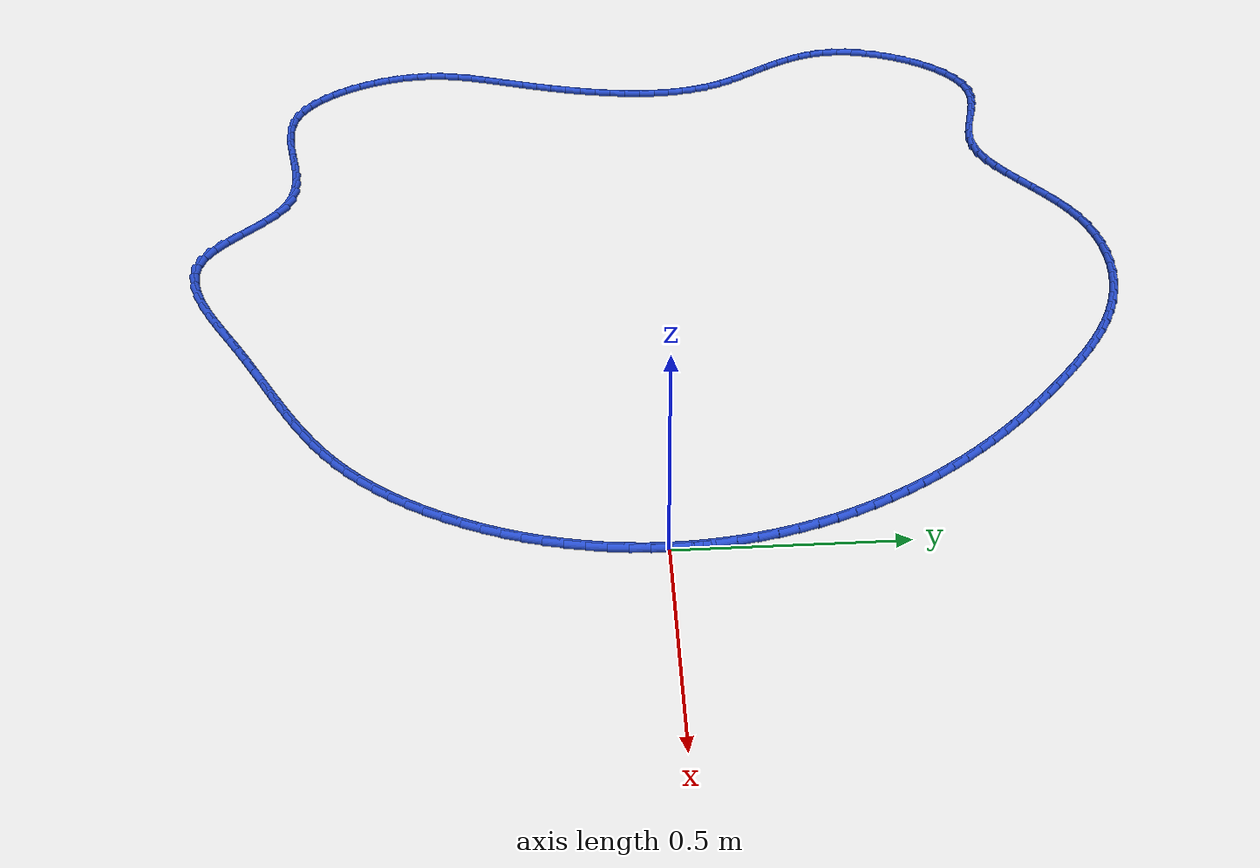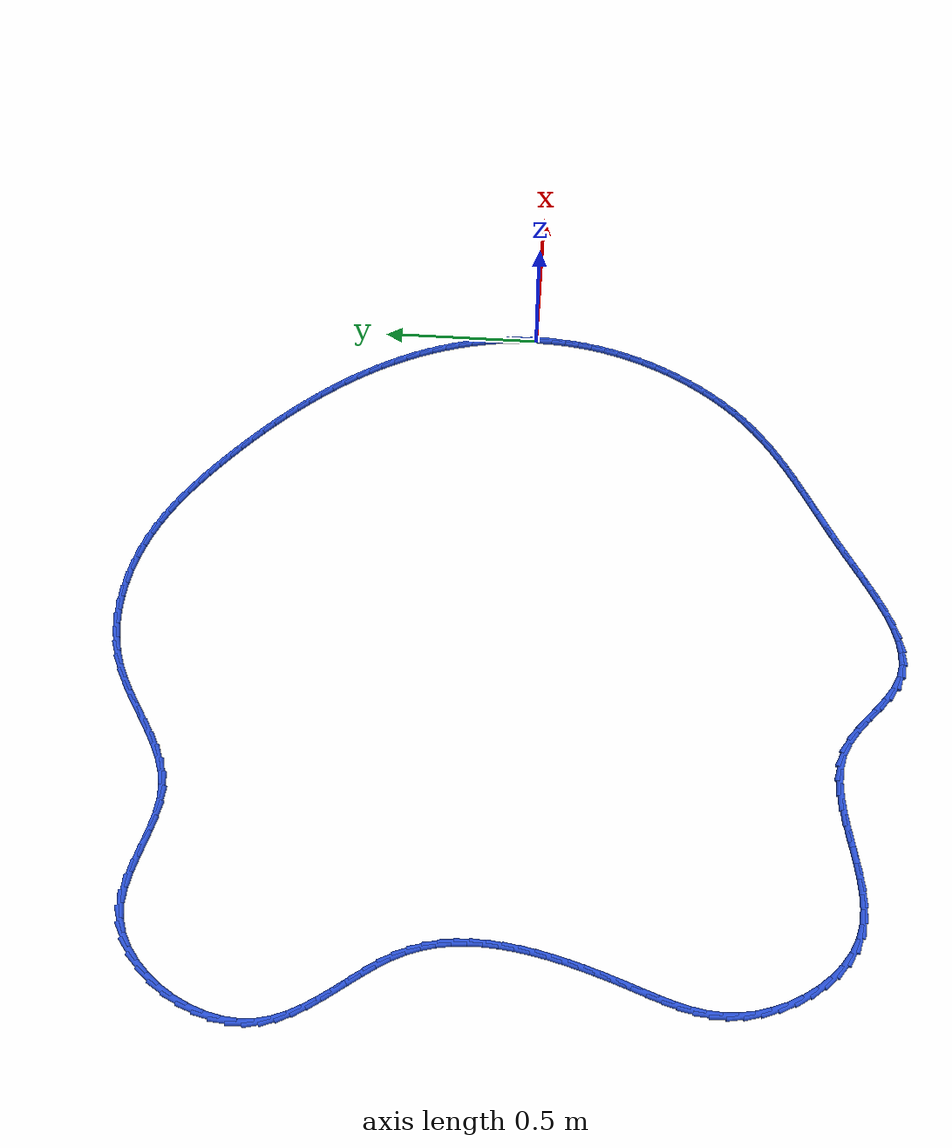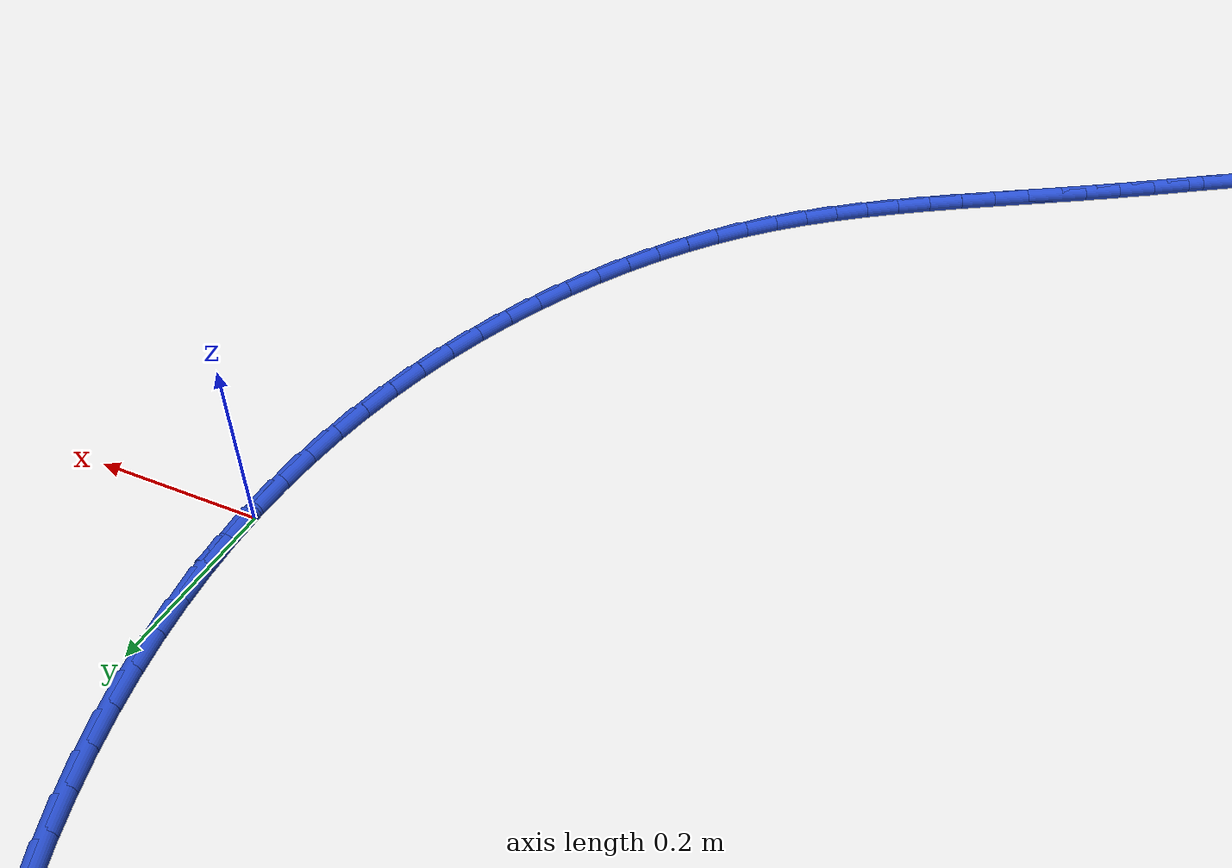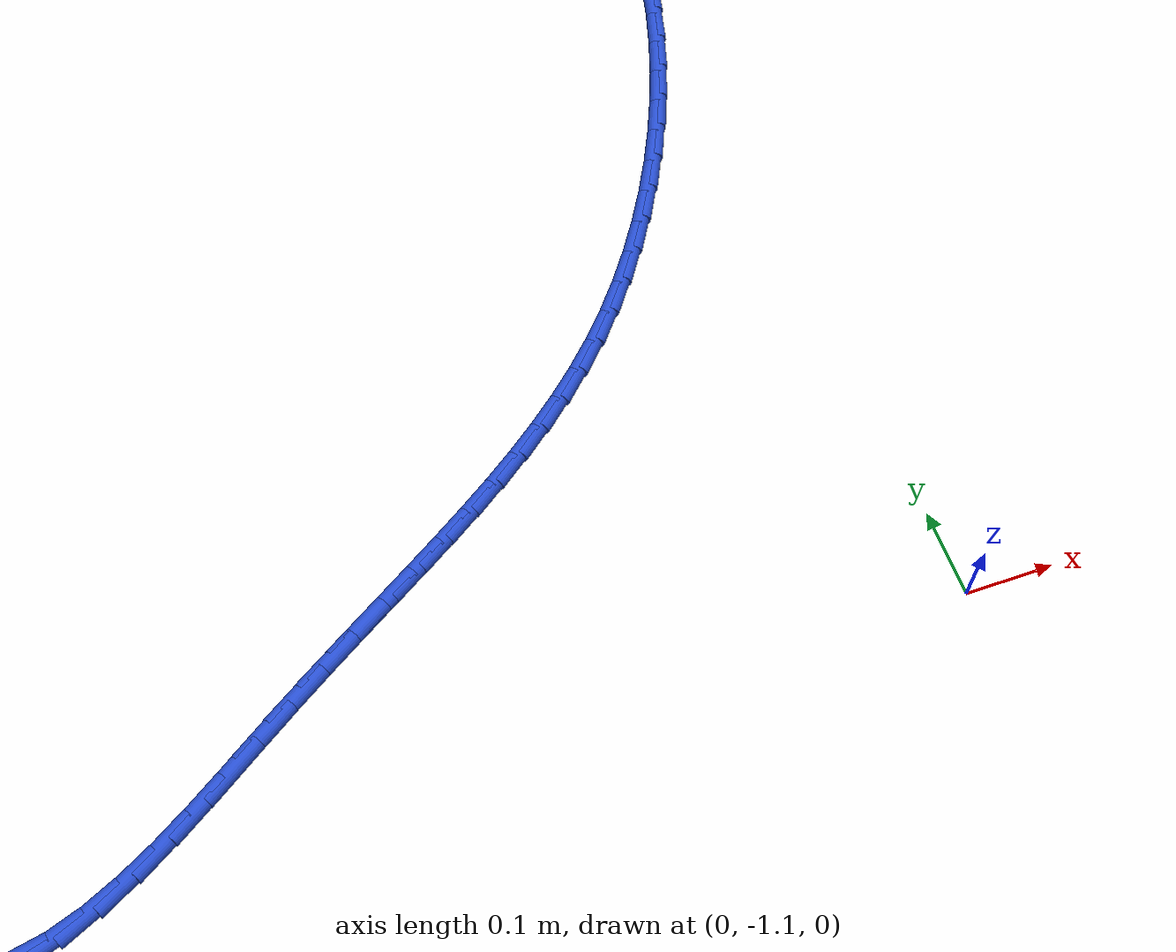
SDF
<sdf version="1.6">
 <world name="default">
  <light name="sun" type="directional">
   <pose>0 0 10 0 -0 0</pose>
   <diffuse>0.8 0.8 0.8 1</diffuse>
   <specular>0.2 0.2 0.2 1</specular>
   <attenuation>
    <range>1000</range>
    <constant>0.9</constant>
    <linear>0.01</linear>
    <quadratic>0.001</quadratic>
   </attenuation>
   <direction>-0.5 0.1 -0.9</direction>
  </light>
  <model name="ground_plane">
   <static>1</static>
   <link name="link">
    <collision name="collision">
     <geometry><plane><normal>0 0 1</normal><size>100 100</size></plane></geometry>
     <surface><friction><ode><mu>100</mu><mu2>50</mu2></ode></friction></surface>
    </collision>
    <visual name="visual">
     <cast_shadows>0</cast_shadows>
     <geometry><plane><normal>0 0 1</normal><size>100 100</size></plane></geometry>
     <material>
      <script><uri>file://media/materials/scripts/gazebo.material</uri><name>Gazebo/WhiteGlow</name></script>
     </material>
    </visual>
   </link>
  </model>
  <gravity>0 0 -9.8</gravity>
  <magnetic_field>6e-06 2.3e-05 -4.2e-05</magnetic_field>
  <atmosphere type="adiabatic"/>
  <physics name="default_physics" default="0" type="ode">
   <max_step_size>0.001</max_step_size>
   <real_time_factor>1</real_time_factor>
   <real_time_update_rate>1000</real_time_update_rate>
  </physics>
  <scene><ambient>0.4 0.4 0.4 1</ambient><background>0.7 0.7 0.7 1</background><shadows>1</shadows></scene>
  <spherical_coordinates>
   <surface_model>EARTH_WGS84</surface_model>
   <latitude_deg>0</latitude_deg>
   <longitude_deg>0</longitude_deg>
   <elevation>0</elevation>
   <heading_deg>0</heading_deg>
  </spherical_coordinates>
  <model name="line">
   <link name="link_0">
    <pose>3.469446951953614e-18 6.938893903907228e-18 0.01 0 1.57 -1.5439821003446859</pose>
    <collision name="collision">
     <geometry><cylinder><radius>0.01</radius><length>0.08</length></cylinder></geometry>
    </collision>
    <visual name="visual">
     <material>
      <script><name>Gazebo/Blue</name><uri>file://media/materials/scripts/gazebo.material</uri></script>
     </material>
     <geometry><cylinder><radius>0.01</radius><length>0.08</length></cylinder></geometry>
    </visual>
   </link>
   <link name="link_1">
    <pose>-0.0011839507488305542 0.04414324548259012 0.01 0 1.57 -1.499096872646493</pose>
    <collision name="collision">
     <geometry><cylinder><radius>0.01</radius><length>0.08</length></cylinder></geometry>
    </collision>
    <visual name="visual">
     <material>
      <script><name>Gazebo/Blue</name><uri>file://media/materials/scripts/gazebo.material</uri></script>
     </material>
     <geometry><cylinder><radius>0.01</radius><length>0.08</length></cylinder></geometry>
    </visual>
   </link>
   <link name="link_2">
    <pose>-0.00435128964356094 0.08824273699094067 0.01 0 1.57 -1.4552568356801363</pose>
    <collision name="collision">
     <geometry><cylinder><radius>0.01</radius><length>0.08</length></cylinder></geometry>
    </collision>
    <visual name="visual">
     <material>
      <script><name>Gazebo/Blue</name><uri>file://media/materials/scripts/gazebo.material</uri></script>
     </material>
     <geometry><cylinder><radius>0.01</radius><length>0.08</length></cylinder></geometry>
    </visual>
   </link>
   <link name="link_3">
    <pose>-0.009453980212633106 0.13221007992053202 0.01 0 1.57 -1.412352412987002</pose>
    <collision name="collision">
     <geometry><cylinder><radius>0.01</radius><length>0.08</length></cylinder></geometry>
    </collision>
    <visual name="visual">
     <material>
      <script><name>Gazebo/Blue</name><uri>file://media/materials/scripts/gazebo.material</uri></script>
     </material>
     <geometry><cylinder><radius>0.01</radius><length>0.08</length></cylinder></geometry>
    </visual>
   </link>
   <link name="link_4">
    <pose>-0.016443985984489005 0.17595687966684467 0.01 0 1.57 -1.3702658114433748</pose>
    <collision name="collision">
     <geometry><cylinder><radius>0.01</radius><length>0.08</length></cylinder></geometry>
    </collision>
    <visual name="visual">
     <material>
      <script><name>Gazebo/Blue</name><uri>file://media/materials/scripts/gazebo.material</uri></script>
     </material>
     <geometry><cylinder><radius>0.01</radius><length>0.08</length></cylinder></geometry>
    </visual>
   </link>
   <link name="link_5">
    <pose>-0.025273270487570585 0.21939474162535907 0.01 0 1.57 -1.3288727719784204</pose>
    <collision name="collision">
     <geometry><cylinder><radius>0.01</radius><length>0.08</length></cylinder></geometry>
    </collision>
    <visual name="visual">
     <material>
      <script><name>Gazebo/Blue</name><uri>file://media/materials/scripts/gazebo.material</uri></script>
     </material>
     <geometry><cylinder><radius>0.01</radius><length>0.08</length></cylinder></geometry>
    </visual>
   </link>
   <link name="link_6">
    <pose>-0.03589379725031978 0.2624352711915555 0.01 0 1.57 -1.2880438969504369</pose>
    <collision name="collision">
     <geometry><cylinder><radius>0.01</radius><length>0.08</length></cylinder></geometry>
    </collision>
    <visual name="visual">
     <material>
      <script><name>Gazebo/Blue</name><uri>file://media/materials/scripts/gazebo.material</uri></script>
     </material>
     <geometry><cylinder><radius>0.01</radius><length>0.08</length></cylinder></geometry>
    </visual>
   </link>
   <link name="link_7">
    <pose>-0.04825752980117855 0.30499007376091464 0.01 0 1.57 -1.247645606803307</pose>
    <collision name="collision">
     <geometry><cylinder><radius>0.01</radius><length>0.08</length></cylinder></geometry>
    </collision>
    <visual name="visual">
     <material>
      <script><name>Gazebo/Blue</name><uri>file://media/materials/scripts/gazebo.material</uri></script>
     </material>
     <geometry><cylinder><radius>0.01</radius><length>0.08</length></cylinder></geometry>
    </visual>
   </link>
   <link name="link_8">
    <pose>-0.062316431668588815 0.34697075472891664 0.01 0 1.57 -1.2075959212951473</pose>
    <collision name="collision">
     <geometry><cylinder><radius>0.01</radius><length>0.08</length></cylinder></geometry>
    </collision>
    <visual name="visual">
     <material>
      <script><name>Gazebo/Blue</name><uri>file://media/materials/scripts/gazebo.material</uri></script>
     </material>
     <geometry><cylinder><radius>0.01</radius><length>0.08</length></cylinder></geometry>
    </visual>
   </link>
   <link name="link_9">
    <pose>-0.07802146258468275 0.3882931384778241 0.01 0 1.57 -1.1684688636281626</pose>
    <collision name="collision">
     <geometry><cylinder><radius>0.01</radius><length>0.08</length></cylinder></geometry>
    </collision>
    <visual name="visual">
     <material>
      <script><name>Gazebo/Blue</name><uri>file://media/materials/scripts/gazebo.material</uri></script>
     </material>
     <geometry><cylinder><radius>0.01</radius><length>0.08</length></cylinder></geometry>
    </visual>
   </link>
   <link name="link_10">
    <pose>-0.09531147299239753 0.42892394510504833 0.01 0 1.57 -1.130735102965538</pose>
    <collision name="collision">
     <geometry><cylinder><radius>0.01</radius><length>0.08</length></cylinder></geometry>
    </collision>
    <visual name="visual">
     <material>
      <script><name>Gazebo/Blue</name><uri>file://media/materials/scripts/gazebo.material</uri></script>
     </material>
     <geometry><cylinder><radius>0.01</radius><length>0.08</length></cylinder></geometry>
    </visual>
   </link>
   <link name="link_11">
    <pose>-0.11411728667674684 0.4688636309982726 0.01 0 1.57 -1.09444106113894</pose>
    <collision name="collision">
     <geometry><cylinder><radius>0.01</radius><length>0.08</length></cylinder></geometry>
    </collision>
    <visual name="visual">
     <material>
      <script><name>Gazebo/Blue</name><uri>file://media/materials/scripts/gazebo.material</uri></script>
     </material>
     <geometry><cylinder><radius>0.01</radius><length>0.08</length></cylinder></geometry>
    </visual>
   </link>
   <link name="link_12">
    <pose>-0.1343695836832227 0.5081132566868144 0.01 0 1.57 -1.0596072428523382</pose>
    <collision name="collision">
     <geometry><cylinder><radius>0.01</radius><length>0.08</length></cylinder></geometry>
    </collision>
    <visual name="visual">
     <material>
      <script><name>Gazebo/Blue</name><uri>file://media/materials/scripts/gazebo.material</uri></script>
     </material>
     <geometry><cylinder><radius>0.01</radius><length>0.08</length></cylinder></geometry>
    </visual>
   </link>
   <link name="link_13">
    <pose>-0.1559990440573169 0.5466738826999911 0.01 0 1.57 -1.026238351442877</pose>
    <collision name="collision">
     <geometry><cylinder><radius>0.01</radius><length>0.08</length></cylinder></geometry>
    </collision>
    <visual name="visual">
     <material>
      <script><name>Gazebo/Blue</name><uri>file://media/materials/scripts/gazebo.material</uri></script>
     </material>
     <geometry><cylinder><radius>0.01</radius><length>0.08</length></cylinder></geometry>
    </visual>
   </link>
   <link name="link_14">
    <pose>-0.1789363478445213 0.5845465695671197 0.01 0 1.57 -0.9943256076428734</pose>
    <collision name="collision">
     <geometry><cylinder><radius>0.01</radius><length>0.08</length></cylinder></geometry>
    </collision>
    <visual name="visual">
     <material>
      <script><name>Gazebo/Blue</name><uri>file://media/materials/scripts/gazebo.material</uri></script>
     </material>
     <geometry><cylinder><radius>0.01</radius><length>0.08</length></cylinder></geometry>
    </visual>
   </link>
   <link name="link_15">
    <pose>-0.2031121750903279 0.6217323778175178 0.01 0 1.57 -0.9638490437568503</pose>
    <collision name="collision">
     <geometry><cylinder><radius>0.01</radius><length>0.08</length></cylinder></geometry>
    </collision>
    <visual name="visual">
     <material>
      <script><name>Gazebo/Blue</name><uri>file://media/materials/scripts/gazebo.material</uri></script>
     </material>
     <geometry><cylinder><radius>0.01</radius><length>0.08</length></cylinder></geometry>
    </visual>
   </link>
   <link name="link_16">
    <pose>-0.22845720584022855 0.6582323679805026 0.01 0 1.57 -0.9347796829185863</pose>
    <collision name="collision">
     <geometry><cylinder><radius>0.01</radius><length>0.08</length></cylinder></geometry>
    </collision>
    <visual name="visual">
     <material>
      <script><name>Gazebo/Blue</name><uri>file://media/materials/scripts/gazebo.material</uri></script>
     </material>
     <geometry><cylinder><radius>0.01</radius><length>0.08</length></cylinder></geometry>
    </visual>
   </link>
   <link name="link_17">
    <pose>-0.2549021201397152 0.6940476005853915 0.01 0 1.57 -0.9070815428317615</pose>
    <collision name="collision">
     <geometry><cylinder><radius>0.01</radius><length>0.08</length></cylinder></geometry>
    </collision>
    <visual name="visual">
     <material>
      <script><name>Gazebo/Blue</name><uri>file://media/materials/scripts/gazebo.material</uri></script>
     </material>
     <geometry><cylinder><radius>0.01</radius><length>0.08</length></cylinder></geometry>
    </visual>
   </link>
   <link name="link_18">
    <pose>-0.28237759803427964 0.7291791361615019 0.01 0 1.57 -0.8807134289384356</pose>
    <collision name="collision">
     <geometry><cylinder><radius>0.01</radius><length>0.08</length></cylinder></geometry>
    </collision>
    <visual name="visual">
     <material>
      <script><name>Gazebo/Blue</name><uri>file://media/materials/scripts/gazebo.material</uri></script>
     </material>
     <geometry><cylinder><radius>0.01</radius><length>0.08</length></cylinder></geometry>
    </visual>
   </link>
   <link name="link_19">
    <pose>-0.3108143195694138 0.7636280352381509 0.01 0 1.57 -0.8556305024046496</pose>
    <collision name="collision">
     <geometry><cylinder><radius>0.01</radius><length>0.08</length></cylinder></geometry>
    </collision>
    <visual name="visual">
     <material>
      <script><name>Gazebo/Blue</name><uri>file://media/materials/scripts/gazebo.material</uri></script>
     </material>
     <geometry><cylinder><radius>0.01</radius><length>0.08</length></cylinder></geometry>
    </visual>
   </link>
   <link name="link_20">
    <pose>-0.3401429647906097 0.7973953583446561 0.01 0 1.57 -0.8317856236187741</pose>
    <collision name="collision">
     <geometry><cylinder><radius>0.01</radius><length>0.08</length></cylinder></geometry>
    </collision>
    <visual name="visual">
     <material>
      <script><name>Gazebo/Blue</name><uri>file://media/materials/scripts/gazebo.material</uri></script>
     </material>
     <geometry><cylinder><radius>0.01</radius><length>0.08</length></cylinder></geometry>
    </visual>
   </link>
   <link name="link_21">
    <pose>-0.370294213743359 0.8304821660103344 0.01 0 1.57 -0.8091304825563828</pose>
    <collision name="collision">
     <geometry><cylinder><radius>0.01</radius><length>0.08</length></cylinder></geometry>
    </collision>
    <visual name="visual">
     <material>
      <script><name>Gazebo/Blue</name><uri>file://media/materials/scripts/gazebo.material</uri></script>
     </material>
     <geometry><cylinder><radius>0.01</radius><length>0.08</length></cylinder></geometry>
    </visual>
   </link>
   <link name="link_22">
    <pose>-0.4011987464731539 0.8628895187645036 0.01 0 1.57 -0.7876165341358324</pose>
    <collision name="collision">
     <geometry><cylinder><radius>0.01</radius><length>0.08</length></cylinder></geometry>
    </collision>
    <visual name="visual">
     <material>
      <script><name>Gazebo/Blue</name><uri>file://media/materials/scripts/gazebo.material</uri></script>
     </material>
     <geometry><cylinder><radius>0.01</radius><length>0.08</length></cylinder></geometry>
    </visual>
   </link>
   <link name="link_23">
    <pose>-0.4327872430254861 0.894618477136481 0.01 0 1.57 -0.7671957604122086</pose>
    <collision name="collision">
     <geometry><cylinder><radius>0.01</radius><length>0.08</length></cylinder></geometry>
    </collision>
    <visual name="visual">
     <material>
      <script><name>Gazebo/Blue</name><uri>file://media/materials/scripts/gazebo.material</uri></script>
     </material>
     <geometry><cylinder><radius>0.01</radius><length>0.08</length></cylinder></geometry>
    </visual>
   </link>
   <link name="link_24">
    <pose>-0.4649903834458474 0.9256701016555833 0.01 0 1.57 -0.7478212829336518</pose>
    <collision name="collision">
     <geometry><cylinder><radius>0.01</radius><length>0.08</length></cylinder></geometry>
    </collision>
    <visual name="visual">
     <material>
      <script><name>Gazebo/Blue</name><uri>file://media/materials/scripts/gazebo.material</uri></script>
     </material>
     <geometry><cylinder><radius>0.01</radius><length>0.08</length></cylinder></geometry>
    </visual>
   </link>
   <link name="link_25">
    <pose>-0.4977388477797301 0.9560454528511286 0.01 0 1.57 -0.7294476148972723</pose>
    <collision name="collision">
     <geometry><cylinder><radius>0.01</radius><length>0.08</length></cylinder></geometry>
    </collision>
    <visual name="visual">
     <material>
      <script><name>Gazebo/Blue</name><uri>file://media/materials/scripts/gazebo.material</uri></script>
     </material>
     <geometry><cylinder><radius>0.01</radius><length>0.08</length></cylinder></geometry>
    </visual>
   </link>
   <link name="link_26">
    <pose>-0.5309633232596699 0.9857455837131669 0.01 0 1.57 -0.7104372396460971</pose>
    <collision name="collision">
     <geometry><cylinder><radius>0.01</radius><length>0.08</length></cylinder></geometry>
    </collision>
    <visual name="visual">
     <material>
      <script><name>Gazebo/Blue</name><uri>file://media/materials/scripts/gazebo.material</uri></script>
     </material>
     <geometry><cylinder><radius>0.01</radius><length>0.08</length></cylinder></geometry>
    </visual>
   </link>
   <link name="link_27">
    <pose>-0.5646434299057079 1.0147202163492524 0.01 0 1.57 -0.6853254959440181</pose>
    <collision name="collision">
     <geometry><cylinder><radius>0.01</radius><length>0.08</length></cylinder></geometry>
    </collision>
    <visual name="visual">
     <material>
      <script><name>Gazebo/Blue</name><uri>file://media/materials/scripts/gazebo.material</uri></script>
     </material>
     <geometry><cylinder><radius>0.01</radius><length>0.08</length></cylinder></geometry>
    </visual>
   </link>
   <link name="link_28">
    <pose>-0.5989244939661343 1.0427452457182091 0.01 0 1.57 -0.6528852414257819</pose>
    <collision name="collision">
     <geometry><cylinder><radius>0.01</radius><length>0.08</length></cylinder></geometry>
    </collision>
    <visual name="visual">
     <material>
      <script><name>Gazebo/Blue</name><uri>file://media/materials/scripts/gazebo.material</uri></script>
     </material>
     <geometry><cylinder><radius>0.01</radius><length>0.08</length></cylinder></geometry>
    </visual>
   </link>
   <link name="link_29">
    <pose>-0.6339868840030394 1.0695598071135357 0.01 0 1.57 -0.6130763934777326</pose>
    <collision name="collision">
     <geometry><cylinder><radius>0.01</radius><length>0.08</length></cylinder></geometry>
    </collision>
    <visual name="visual">
     <material>
      <script><name>Gazebo/Blue</name><uri>file://media/materials/scripts/gazebo.material</uri></script>
     </material>
     <geometry><cylinder><radius>0.01</radius><length>0.08</length></cylinder></geometry>
    </visual>
   </link>
   <link name="link_30">
    <pose>-0.6700109685785137 1.0949030358287302 0.01 0 1.57 -0.5659598649628423</pose>
    <collision name="collision">
     <geometry><cylinder><radius>0.01</radius><length>0.08</length></cylinder></geometry>
    </collision>
    <visual name="visual">
     <material>
      <script><name>Gazebo/Blue</name><uri>file://media/materials/scripts/gazebo.material</uri></script>
     </material>
     <geometry><cylinder><radius>0.01</radius><length>0.08</length></cylinder></geometry>
    </visual>
   </link>
   <link name="link_31">
    <pose>-0.7071771162546483 1.1185140671572917 0.01 0 1.57 -0.5117604876687721</pose>
    <collision name="collision">
     <geometry><cylinder><radius>0.01</radius><length>0.08</length></cylinder></geometry>
    </collision>
    <visual name="visual">
     <material>
      <script><name>Gazebo/Blue</name><uri>file://media/materials/scripts/gazebo.material</uri></script>
     </material>
     <geometry><cylinder><radius>0.01</radius><length>0.08</length></cylinder></geometry>
    </visual>
   </link>
   <link name="link_32">
    <pose>-0.7456656955935332 1.1401320363927179 0.01 0 1.57 -0.45093228981901173</pose>
    <collision name="collision">
     <geometry><cylinder><radius>0.01</radius><length>0.08</length></cylinder></geometry>
    </collision>
    <visual name="visual">
     <material>
      <script><name>Gazebo/Blue</name><uri>file://media/materials/scripts/gazebo.material</uri></script>
     </material>
     <geometry><cylinder><radius>0.01</radius><length>0.08</length></cylinder></geometry>
    </visual>
   </link>
   <link name="link_33">
    <pose>-0.7856570748833374 1.1594960788533608 0.01 0 1.57 -0.38509504547642065</pose>
    <collision name="collision">
     <geometry><cylinder><radius>0.01</radius><length>0.08</length></cylinder></geometry>
    </collision>
    <visual name="visual">
     <material>
      <script><name>Gazebo/Blue</name><uri>file://media/materials/scripts/gazebo.material</uri></script>
     </material>
     <geometry><cylinder><radius>0.01</radius><length>0.08</length></cylinder></geometry>
    </visual>
   </link>
   <link name="link_34">
    <pose>-0.8272453328819714 1.176353158953246 0.01 0 1.57 -0.3177773301988854</pose>
    <collision name="collision">
     <geometry><cylinder><radius>0.01</radius><length>0.08</length></cylinder></geometry>
    </collision>
    <visual name="visual">
     <material>
      <script><name>Gazebo/Blue</name><uri>file://media/materials/scripts/gazebo.material</uri></script>
     </material>
     <geometry><cylinder><radius>0.01</radius><length>0.08</length></cylinder></geometry>
    </visual>
   </link>
   <link name="link_35">
    <pose>-0.8701944909436155 1.1904801873928645 0.01 0 1.57 -0.24887371815468787</pose>
    <collision name="collision">
     <geometry><cylinder><radius>0.01</radius><length>0.08</length></cylinder></geometry>
    </collision>
    <visual name="visual">
     <material>
      <script><name>Gazebo/Blue</name><uri>file://media/materials/scripts/gazebo.material</uri></script>
     </material>
     <geometry><cylinder><radius>0.01</radius><length>0.08</length></cylinder></geometry>
    </visual>
   </link>
   <link name="link_36">
    <pose>-0.9141896674780737 1.2016612337794539 0.01 0 1.57 -0.1774084540356563</pose>
    <collision name="collision">
     <geometry><cylinder><radius>0.01</radius><length>0.08</length></cylinder></geometry>
    </collision>
    <visual name="visual">
     <material>
      <script><name>Gazebo/Blue</name><uri>file://media/materials/scripts/gazebo.material</uri></script>
     </material>
     <geometry><cylinder><radius>0.01</radius><length>0.08</length></cylinder></geometry>
    </visual>
   </link>
   <link name="link_37">
    <pose>-0.9589159808951517 1.2096803677202537 0.01 0 1.57 -0.10245407456369696</pose>
    <collision name="collision">
     <geometry><cylinder><radius>0.01</radius><length>0.08</length></cylinder></geometry>
    </collision>
    <visual name="visual">
     <material>
      <script><name>Gazebo/Blue</name><uri>file://media/materials/scripts/gazebo.material</uri></script>
     </material>
     <geometry><cylinder><radius>0.01</radius><length>0.08</length></cylinder></geometry>
    </visual>
   </link>
   <link name="link_38">
    <pose>-1.0040585496046535 1.2143216588225014 0.01 0 1.57 -0.02314853000692653</pose>
    <collision name="collision">
     <geometry><cylinder><radius>0.01</radius><length>0.08</length></cylinder></geometry>
    </collision>
    <visual name="visual">
     <material>
      <script><name>Gazebo/Blue</name><uri>file://media/materials/scripts/gazebo.material</uri></script>
     </material>
     <geometry><cylinder><radius>0.01</radius><length>0.08</length></cylinder></geometry>
    </visual>
   </link>
   <link name="link_39">
    <pose>-1.0493024920163843 1.2153691766934367 0.01 0 1.57 0.06126365880684225</pose>
    <collision name="collision">
     <geometry><cylinder><radius>0.01</radius><length>0.08</length></cylinder></geometry>
    </collision>
    <visual name="visual">
     <material>
      <script><name>Gazebo/Blue</name><uri>file://media/materials/scripts/gazebo.material</uri></script>
     </material>
     <geometry><cylinder><radius>0.01</radius><length>0.08</length></cylinder></geometry>
    </visual>
   </link>
   <link name="link_40">
    <pose>-1.0943329265401494 1.2126069909402981 0.01 0 1.57 0.15136165774012475</pose>
    <collision name="collision">
     <geometry><cylinder><radius>0.01</radius><length>0.08</length></cylinder></geometry>
    </collision>
    <visual name="visual">
     <material>
      <script><name>Gazebo/Blue</name><uri>file://media/materials/scripts/gazebo.material</uri></script>
     </material>
     <geometry><cylinder><radius>0.01</radius><length>0.08</length></cylinder></geometry>
    </visual>
   </link>
   <link name="link_41">
    <pose>-1.138834971585753 1.205819171170324 0.01 0 1.57 0.24744958167394657</pose>
    <collision name="collision">
     <geometry><cylinder><radius>0.01</radius><length>0.08</length></cylinder></geometry>
    </collision>
    <visual name="visual">
     <material>
      <script><name>Gazebo/Blue</name><uri>file://media/materials/scripts/gazebo.material</uri></script>
     </material>
     <geometry><cylinder><radius>0.01</radius><length>0.08</length></cylinder></geometry>
    </visual>
   </link>
   <link name="link_42">
    <pose>-1.1824937455630005 1.1947897869907533 0.01 0 1.57 0.3493568819548985</pose>
    <collision name="collision">
     <geometry><cylinder><radius>0.01</radius><length>0.08</length></cylinder></geometry>
    </collision>
    <visual name="visual">
     <material>
      <script><name>Gazebo/Blue</name><uri>file://media/materials/scripts/gazebo.material</uri></script>
     </material>
     <geometry><cylinder><radius>0.01</radius><length>0.08</length></cylinder></geometry>
    </visual>
   </link>
   <link name="link_43">
    <pose>-1.2249957215201597 1.1793063233141308 0.01 0 1.57 0.44572407763373284</pose>
    <collision name="collision">
     <geometry><cylinder><radius>0.01</radius><length>0.08</length></cylinder></geometry>
    </collision>
    <visual name="visual">
     <material>
      <script><name>Gazebo/Blue</name><uri>file://media/materials/scripts/gazebo.material</uri></script>
     </material>
     <geometry><cylinder><radius>0.01</radius><length>0.08</length></cylinder></geometry>
    </visual>
   </link>
   <link name="link_44">
    <pose>-1.266209252113946 1.159614818688168 0.01 0 1.57 0.5152087284668984</pose>
    <collision name="collision">
     <geometry><cylinder><radius>0.01</radius><length>0.08</length></cylinder></geometry>
    </collision>
    <visual name="visual">
     <material>
      <script><name>Gazebo/Blue</name><uri>file://media/materials/scripts/gazebo.material</uri></script>
     </material>
     <geometry><cylinder><radius>0.01</radius><length>0.08</length></cylinder></geometry>
    </visual>
   </link>
   <link name="link_45">
    <pose>-1.306366029375413 1.136877360426707 0.01 0 1.57 0.55682797016728</pose>
    <collision name="collision">
     <geometry><cylinder><radius>0.01</radius><length>0.08</length></cylinder></geometry>
    </collision>
    <visual name="visual">
     <material>
      <script><name>Gazebo/Blue</name><uri>file://media/materials/scripts/gazebo.material</uri></script>
     </material>
     <geometry><cylinder><radius>0.01</radius><length>0.08</length></cylinder></geometry>
    </visual>
   </link>
   <link name="link_46">
    <pose>-1.3457409360228434 1.112364927911284 0.01 0 1.57 0.5718817607722702</pose>
    <collision name="collision">
     <geometry><cylinder><radius>0.01</radius><length>0.08</length></cylinder></geometry>
    </collision>
    <visual name="visual">
     <material>
      <script><name>Gazebo/Blue</name><uri>file://media/materials/scripts/gazebo.material</uri></script>
     </material>
     <geometry><cylinder><radius>0.01</radius><length>0.08</length></cylinder></geometry>
    </visual>
   </link>
   <link name="link_47">
    <pose>-1.384608854774522 1.0873485005234345 0.01 0 1.57 0.5604966200062869</pose>
    <collision name="collision">
     <geometry><cylinder><radius>0.01</radius><length>0.08</length></cylinder></geometry>
    </collision>
    <visual name="visual">
     <material>
      <script><name>Gazebo/Blue</name><uri>file://media/materials/scripts/gazebo.material</uri></script>
     </material>
     <geometry><cylinder><radius>0.01</radius><length>0.08</length></cylinder></geometry>
    </visual>
   </link>
   <link name="link_48">
    <pose>-1.4232446683487323 1.0630990576446957 0.01 0 1.57 0.5212762469050544</pose>
    <collision name="collision">
     <geometry><cylinder><radius>0.01</radius><length>0.08</length></cylinder></geometry>
    </collision>
    <visual name="visual">
     <material>
      <script><name>Gazebo/Blue</name><uri>file://media/materials/scripts/gazebo.material</uri></script>
     </material>
     <geometry><cylinder><radius>0.01</radius><length>0.08</length></cylinder></geometry>
    </visual>
   </link>
   <link name="link_49">
    <pose>-1.4619232594637588 1.0408875786566039 0.01 0 1.57 0.4513547201303458</pose>
    <collision name="collision">
     <geometry><cylinder><radius>0.01</radius><length>0.08</length></cylinder></geometry>
    </collision>
    <visual name="visual">
     <material>
      <script><name>Gazebo/Blue</name><uri>file://media/materials/scripts/gazebo.material</uri></script>
     </material>
     <geometry><cylinder><radius>0.01</radius><length>0.08</length></cylinder></geometry>
    </visual>
   </link>
   <link name="link_50">
    <pose>-1.5009195108378854 1.021985042940695 0.01 0 1.57 0.34713446402082365</pose>
    <collision name="collision">
     <geometry><cylinder><radius>0.01</radius><length>0.08</length></cylinder></geometry>
    </collision>
    <visual name="visual">
     <material>
      <script><name>Gazebo/Blue</name><uri>file://media/materials/scripts/gazebo.material</uri></script>
     </material>
     <geometry><cylinder><radius>0.01</radius><length>0.08</length></cylinder></geometry>
    </visual>
   </link>
   <link name="link_51">
    <pose>-1.5405083051893957 1.0076624298785057 0.01 0 1.57 0.20642169532118823</pose>
    <collision name="collision">
     <geometry><cylinder><radius>0.01</radius><length>0.08</length></cylinder></geometry>
    </collision>
    <visual name="visual">
     <material>
      <script><name>Gazebo/Blue</name><uri>file://media/materials/scripts/gazebo.material</uri></script>
     </material>
     <geometry><cylinder><radius>0.01</radius><length>0.08</length></cylinder></geometry>
    </visual>
   </link>
   <link name="link_52">
    <pose>-1.5809645252365747 0.9991907188515722 0.01 0 1.57 0.0340555826025112</pose>
    <collision name="collision">
     <geometry><cylinder><radius>0.01</radius><length>0.08</length></cylinder></geometry>
    </collision>
    <visual name="visual">
     <material>
      <script><name>Gazebo/Blue</name><uri>file://media/materials/scripts/gazebo.material</uri></script>
     </material>
     <geometry><cylinder><radius>0.01</radius><length>0.08</length></cylinder></geometry>
    </visual>
   </link>
   <link name="link_53">
    <pose>-1.6225514629047713 0.9977739036856969 0.01 0 1.57 -0.12243299148436901</pose>
    <collision name="collision">
     <geometry><cylinder><radius>0.01</radius><length>0.08</length></cylinder></geometry>
    </collision>
    <visual name="visual">
     <material>
      <script><name>Gazebo/Blue</name><uri>file://media/materials/scripts/gazebo.material</uri></script>
     </material>
     <geometry><cylinder><radius>0.01</radius><length>0.08</length></cylinder></geometry>
    </visual>
   </link>
   <link name="link_54">
    <pose>-1.6652577825273638 1.0030288493560866 0.01 0 1.57 -0.22425906854549962</pose>
    <collision name="collision">
     <geometry><cylinder><radius>0.01</radius><length>0.08</length></cylinder></geometry>
    </collision>
    <visual name="visual">
     <material>
      <script><name>Gazebo/Blue</name><uri>file://media/materials/scripts/gazebo.material</uri></script>
     </material>
     <geometry><cylinder><radius>0.01</radius><length>0.08</length></cylinder></geometry>
    </visual>
   </link>
   <link name="link_55">
    <pose>-1.708792978866112 1.012959042960855 0.01 0 1.57 -0.27720434813730616</pose>
    <collision name="collision">
     <geometry><cylinder><radius>0.01</radius><length>0.08</length></cylinder></geometry>
    </collision>
    <visual name="visual">
     <material>
      <script><name>Gazebo/Blue</name><uri>file://media/materials/scripts/gazebo.material</uri></script>
     </material>
     <geometry><cylinder><radius>0.01</radius><length>0.08</length></cylinder></geometry>
    </visual>
   </link>
   <link name="link_56">
    <pose>-1.752854047417289 1.0254957357942611 0.01 0 1.57 -0.28708524317480616</pose>
    <collision name="collision">
     <geometry><cylinder><radius>0.01</radius><length>0.08</length></cylinder></geometry>
    </collision>
    <visual name="visual">
     <material>
      <script><name>Gazebo/Blue</name><uri>file://media/materials/scripts/gazebo.material</uri></script>
     </material>
     <geometry><cylinder><radius>0.01</radius><length>0.08</length></cylinder></geometry>
    </visual>
   </link>
   <link name="link_57">
    <pose>-1.7971379836771666 1.0385701791505635 0.01 0 1.57 -0.2554369536197095</pose>
    <collision name="collision">
     <geometry><cylinder><radius>0.01</radius><length>0.08</length></cylinder></geometry>
    </collision>
    <visual name="visual">
     <material>
      <script><name>Gazebo/Blue</name><uri>file://media/materials/scripts/gazebo.material</uri></script>
     </material>
     <geometry><cylinder><radius>0.01</radius><length>0.08</length></cylinder></geometry>
    </visual>
   </link>
   <link name="link_58">
    <pose>-1.8413417831420185 1.0501136243240223 0.01 0 1.57 -0.17933004626102003</pose>
    <collision name="collision">
     <geometry><cylinder><radius>0.01</radius><length>0.08</length></cylinder></geometry>
    </collision>
    <visual name="visual">
     <material>
      <script><name>Gazebo/Blue</name><uri>file://media/materials/scripts/gazebo.material</uri></script>
     </material>
     <geometry><cylinder><radius>0.01</radius><length>0.08</length></cylinder></geometry>
    </visual>
   </link>
   <link name="link_59">
    <pose>-1.885162441308115 1.0580573226088952 0.01 0 1.57 -0.05269785256373374</pose>
    <collision name="collision">
     <geometry><cylinder><radius>0.01</radius><length>0.08</length></cylinder></geometry>
    </collision>
    <visual name="visual">
     <material>
      <script><name>Gazebo/Blue</name><uri>file://media/materials/scripts/gazebo.material</uri></script>
     </material>
     <geometry><cylinder><radius>0.01</radius><length>0.08</length></cylinder></geometry>
    </visual>
   </link>
   <link name="link_60">
    <pose>-1.9282969536717292 1.060332525299442 0.01 0 1.57 0.1286685791889803</pose>
    <collision name="collision">
     <geometry><cylinder><radius>0.01</radius><length>0.08</length></cylinder></geometry>
    </collision>
    <visual name="visual">
     <material>
      <script><name>Gazebo/Blue</name><uri>file://media/materials/scripts/gazebo.material</uri></script>
     </material>
     <geometry><cylinder><radius>0.01</radius><length>0.08</length></cylinder></geometry>
    </visual>
   </link>
   <link name="link_61">
    <pose>-1.9704415675990403 1.0548797129073708 0.01 0 1.57 0.3357606392606404</pose>
    <collision name="collision">
     <geometry><cylinder><radius>0.01</radius><length>0.08</length></cylinder></geometry>
    </collision>
    <visual name="visual">
     <material>
      <script><name>Gazebo/Blue</name><uri>file://media/materials/scripts/gazebo.material</uri></script>
     </material>
     <geometry><cylinder><radius>0.01</radius><length>0.08</length></cylinder></geometry>
    </visual>
   </link>
   <link name="link_62">
    <pose>-2.011210409565103 1.0406524404973785 0.01 0 1.57 0.5178431912625541</pose>
    <collision name="collision">
     <geometry><cylinder><radius>0.01</radius><length>0.08</length></cylinder></geometry>
    </collision>
    <visual name="visual">
     <material>
      <script><name>Gazebo/Blue</name><uri>file://media/materials/scripts/gazebo.material</uri></script>
     </material>
     <geometry><cylinder><radius>0.01</radius><length>0.08</length></cylinder></geometry>
    </visual>
   </link>
   <link name="link_63">
    <pose>-2.0500624459140013 1.018518377535318 0.01 0 1.57 0.6723725663266519</pose>
    <collision name="collision">
     <geometry><cylinder><radius>0.01</radius><length>0.08</length></cylinder></geometry>
    </collision>
    <visual name="visual">
     <material>
      <script><name>Gazebo/Blue</name><uri>file://media/materials/scripts/gazebo.material</uri></script>
     </material>
     <geometry><cylinder><radius>0.01</radius><length>0.08</length></cylinder></geometry>
    </visual>
   </link>
   <link name="link_64">
    <pose>-2.0864394059952667 0.9895578356090138 0.01 0 1.57 0.8054261930871462</pose>
    <collision name="collision">
     <geometry><cylinder><radius>0.01</radius><length>0.08</length></cylinder></geometry>
    </collision>
    <visual name="visual">
     <material>
      <script><name>Gazebo/Blue</name><uri>file://media/materials/scripts/gazebo.material</uri></script>
     </material>
     <geometry><cylinder><radius>0.01</radius><length>0.08</length></cylinder></geometry>
    </visual>
   </link>
   <link name="link_65">
    <pose>-2.119783019158436 0.9548511263062922 0.01 0 1.57 0.9236871256743018</pose>
    <collision name="collision">
     <geometry><cylinder><radius>0.01</radius><length>0.08</length></cylinder></geometry>
    </collision>
    <visual name="visual">
     <material>
      <script><name>Gazebo/Blue</name><uri>file://media/materials/scripts/gazebo.material</uri></script>
     </material>
     <geometry><cylinder><radius>0.01</radius><length>0.08</length></cylinder></geometry>
    </visual>
   </link>
   <link name="link_66">
    <pose>-2.149535014753044 0.915478561214977 0.01 0 1.57 1.0333390958927844</pose>
    <collision name="collision">
     <geometry><cylinder><radius>0.01</radius><length>0.08</length></cylinder></geometry>
    </collision>
    <visual name="visual">
     <material>
      <script><name>Gazebo/Blue</name><uri>file://media/materials/scripts/gazebo.material</uri></script>
     </material>
     <geometry><cylinder><radius>0.01</radius><length>0.08</length></cylinder></geometry>
    </visual>
   </link>
   <link name="link_67">
    <pose>-2.175137122128622 0.8725204519228932 0.01 0 1.57 1.1400060004814445</pose>
    <collision name="collision">
     <geometry><cylinder><radius>0.01</radius><length>0.08</length></cylinder></geometry>
    </collision>
    <visual name="visual">
     <material>
      <script><name>Gazebo/Blue</name><uri>file://media/materials/scripts/gazebo.material</uri></script>
     </material>
     <geometry><cylinder><radius>0.01</radius><length>0.08</length></cylinder></geometry>
    </visual>
   </link>
   <link name="link_68">
    <pose>-2.196031070634708 0.8270571100178661 0.01 0 1.57 1.2490822807322248</pose>
    <collision name="collision">
     <geometry><cylinder><radius>0.01</radius><length>0.08</length></cylinder></geometry>
    </collision>
    <visual name="visual">
     <material>
      <script><name>Gazebo/Blue</name><uri>file://media/materials/scripts/gazebo.material</uri></script>
     </material>
     <geometry><cylinder><radius>0.01</radius><length>0.08</length></cylinder></geometry>
    </visual>
   </link>
   <link name="link_69">
    <pose>-2.2116585896208325 0.7801688470877205 0.01 0 1.57 1.366159188738537</pose>
    <collision name="collision">
     <geometry><cylinder><radius>0.01</radius><length>0.08</length></cylinder></geometry>
    </collision>
    <visual name="visual">
     <material>
      <script><name>Gazebo/Blue</name><uri>file://media/materials/scripts/gazebo.material</uri></script>
     </material>
     <geometry><cylinder><radius>0.01</radius><length>0.08</length></cylinder></geometry>
    </visual>
   </link>
   <link name="link_70">
    <pose>-2.2214614084365323 0.7329359747202812 0.01 0 1.57 1.497378927149011</pose>
    <collision name="collision">
     <geometry><cylinder><radius>0.01</radius><length>0.08</length></cylinder></geometry>
    </collision>
    <visual name="visual">
     <material>
      <script><name>Gazebo/Blue</name><uri>file://media/materials/scripts/gazebo.material</uri></script>
     </material>
     <geometry><cylinder><radius>0.01</radius><length>0.08</length></cylinder></geometry>
    </visual>
   </link>
   <link name="link_71">
    <pose>-2.2248812564313414 0.686438804503373 0.01 0 1.57 -1.4929736119352088</pose>
    <collision name="collision">
     <geometry><cylinder><radius>0.01</radius><length>0.08</length></cylinder></geometry>
    </collision>
    <visual name="visual">
     <material>
      <script><name>Gazebo/Blue</name><uri>file://media/materials/scripts/gazebo.material</uri></script>
     </material>
     <geometry><cylinder><radius>0.01</radius><length>0.08</length></cylinder></geometry>
    </visual>
   </link>
   <link name="link_72">
    <pose>-2.2213947082353984 0.6417281214554491 0.01 0 1.57 -1.3377265610313767</pose>
    <collision name="collision">
     <geometry><cylinder><radius>0.01</radius><length>0.08</length></cylinder></geometry>
    </collision>
    <visual name="visual">
     <material>
      <script><name>Gazebo/Blue</name><uri>file://media/materials/scripts/gazebo.material</uri></script>
     </material>
     <geometry><cylinder><radius>0.01</radius><length>0.08</length></cylinder></geometry>
    </visual>
   </link>
   <link name="link_73">
    <pose>-2.2112911445245977 0.5991659695752664 0.01 0 1.57 -1.204893047439384</pose>
    <collision name="collision">
     <geometry><cylinder><radius>0.01</radius><length>0.08</length></cylinder></geometry>
    </collision>
    <visual name="visual">
     <material>
      <script><name>Gazebo/Blue</name><uri>file://media/materials/scripts/gazebo.material</uri></script>
     </material>
     <geometry><cylinder><radius>0.01</radius><length>0.08</length></cylinder></geometry>
    </visual>
   </link>
   <link name="link_74">
    <pose>-2.195679116268734 0.5584202590193492 0.01 0 1.57 -1.1004555873983626</pose>
    <collision name="collision">
     <geometry><cylinder><radius>0.01</radius><length>0.08</length></cylinder></geometry>
    </collision>
    <visual name="visual">
     <material>
      <script><name>Gazebo/Blue</name><uri>file://media/materials/scripts/gazebo.material</uri></script>
     </material>
     <geometry><cylinder><radius>0.01</radius><length>0.08</length></cylinder></geometry>
    </visual>
   </link>
   <link name="link_75">
    <pose>-2.1757032925921123 0.5191282947897776 0.01 0 1.57 -1.0251118448766472</pose>
    <collision name="collision">
     <geometry><cylinder><radius>0.01</radius><length>0.08</length></cylinder></geometry>
    </collision>
    <visual name="visual">
     <material>
      <script><name>Gazebo/Blue</name><uri>file://media/materials/scripts/gazebo.material</uri></script>
     </material>
     <geometry><cylinder><radius>0.01</radius><length>0.08</length></cylinder></geometry>
    </visual>
   </link>
   <link name="link_76">
    <pose>-2.1525083426190346 0.4809273818886296 0.01 0 1.57 -0.9774972158469567</pose>
    <collision name="collision">
     <geometry><cylinder><radius>0.01</radius><length>0.08</length></cylinder></geometry>
    </collision>
    <visual name="visual">
     <material>
      <script><name>Gazebo/Blue</name><uri>file://media/materials/scripts/gazebo.material</uri></script>
     </material>
     <geometry><cylinder><radius>0.01</radius><length>0.08</length></cylinder></geometry>
    </visual>
   </link>
   <link name="link_77">
    <pose>-2.1272389354738057 0.443454825317984 0.01 0 1.57 -0.9560237953165027</pose>
    <collision name="collision">
     <geometry><cylinder><radius>0.01</radius><length>0.08</length></cylinder></geometry>
    </collision>
    <visual name="visual">
     <material>
      <script><name>Gazebo/Blue</name><uri>file://media/materials/scripts/gazebo.material</uri></script>
     </material>
     <geometry><cylinder><radius>0.01</radius><length>0.08</length></cylinder></geometry>
    </visual>
   </link>
   <link name="link_78">
    <pose>-2.1010397402807293 0.4063479300799201 0.01 0 1.57 -0.9598612239111127</pose>
    <collision name="collision">
     <geometry><cylinder><radius>0.01</radius><length>0.08</length></cylinder></geometry>
    </collision>
    <visual name="visual">
     <material>
      <script><name>Gazebo/Blue</name><uri>file://media/materials/scripts/gazebo.material</uri></script>
     </material>
     <geometry><cylinder><radius>0.01</radius><length>0.08</length></cylinder></geometry>
    </visual>
   </link>
   <link name="link_79">
    <pose>-2.0750554261641083 0.36924400117651607 0.01 0 1.57 -0.9893082322093759</pose>
    <collision name="collision">
     <geometry><cylinder><radius>0.01</radius><length>0.08</length></cylinder></geometry>
    </collision>
    <visual name="visual">
     <material>
      <script><name>Gazebo/Blue</name><uri>file://media/materials/scripts/gazebo.material</uri></script>
     </material>
     <geometry><cylinder><radius>0.01</radius><length>0.08</length></cylinder></geometry>
    </visual>
   </link>
   <link name="link_80">
    <pose>-2.050430662248247 0.3317803436098515 0.01 0 1.57 -1.045749277015531</pose>
    <collision name="collision">
     <geometry><cylinder><radius>0.01</radius><length>0.08</length></cylinder></geometry>
    </collision>
    <visual name="visual">
     <material>
      <script><name>Gazebo/Blue</name><uri>file://media/materials/scripts/gazebo.material</uri></script>
     </material>
     <geometry><cylinder><radius>0.01</radius><length>0.08</length></cylinder></geometry>
    </visual>
   </link>
   <link name="link_81">
    <pose>-2.0283101176574485 0.2935942623820047 0.01 0 1.57 -1.1308162253469491</pose>
    <collision name="collision">
     <geometry><cylinder><radius>0.01</radius><length>0.08</length></cylinder></geometry>
    </collision>
    <visual name="visual">
     <material>
      <script><name>Gazebo/Blue</name><uri>file://media/materials/scripts/gazebo.material</uri></script>
     </material>
     <geometry><cylinder><radius>0.01</radius><length>0.08</length></cylinder></geometry>
    </visual>
   </link>
   <link name="link_82">
    <pose>-2.0098251655647847 0.2543277559475561 0.01 0 1.57 -1.2315053098989552</pose>
    <collision name="collision">
     <geometry><cylinder><radius>0.01</radius><length>0.08</length></cylinder></geometry>
    </collision>
    <visual name="visual">
     <material>
      <script><name>Gazebo/Blue</name><uri>file://media/materials/scripts/gazebo.material</uri></script>
     </material>
     <geometry><cylinder><radius>0.01</radius><length>0.08</length></cylinder></geometry>
    </visual>
   </link>
   <link name="link_83">
    <pose>-1.9955306231366494 0.21382634623863728 0.01 0 1.57 -1.327370315972428</pose>
    <collision name="collision">
     <geometry><cylinder><radius>0.01</radius><length>0.08</length></cylinder></geometry>
    </collision>
    <visual name="visual">
     <material>
      <script><name>Gazebo/Blue</name><uri>file://media/materials/scripts/gazebo.material</uri></script>
     </material>
     <geometry><cylinder><radius>0.01</radius><length>0.08</length></cylinder></geometry>
    </visual>
   </link>
   <link name="link_84">
    <pose>-1.985195863510464 0.17221281584956116 0.01 0 1.57 -1.4156083627906344</pose>
    <collision name="collision">
     <geometry><cylinder><radius>0.01</radius><length>0.08</length></cylinder></geometry>
    </collision>
    <visual name="visual">
     <material>
      <script><name>Gazebo/Blue</name><uri>file://media/materials/scripts/gazebo.material</uri></script>
     </material>
     <geometry><cylinder><radius>0.01</radius><length>0.08</length></cylinder></geometry>
    </visual>
   </link>
   <link name="link_85">
    <pose>-1.9785339303656495 0.12962983159585945 0.01 0 1.57 -1.4954707841314256</pose>
    <collision name="collision">
     <geometry><cylinder><radius>0.01</radius><length>0.08</length></cylinder></geometry>
    </collision>
    <visual name="visual">
     <material>
      <script><name>Gazebo/Blue</name><uri>file://media/materials/scripts/gazebo.material</uri></script>
     </material>
     <geometry><cylinder><radius>0.01</radius><length>0.08</length></cylinder></geometry>
    </visual>
   </link>
   <link name="link_86">
    <pose>-1.9752578673816266 0.08622006029306234 0.01 0 1.57 -1.5667788045362327</pose>
    <collision name="collision">
     <geometry><cylinder><radius>0.01</radius><length>0.08</length></cylinder></geometry>
    </collision>
    <visual name="visual">
     <material>
      <script><name>Gazebo/Blue</name><uri>file://media/materials/scripts/gazebo.material</uri></script>
     </material>
     <geometry><cylinder><radius>0.01</radius><length>0.08</length></cylinder></geometry>
    </visual>
   </link>
   <link name="link_87">
    <pose>-1.975080718237816 0.042126168756700874 0.01 0 1.57 1.5118351059897275</pose>
    <collision name="collision">
     <geometry><cylinder><radius>0.01</radius><length>0.08</length></cylinder></geometry>
    </collision>
    <visual name="visual">
     <material>
      <script><name>Gazebo/Blue</name><uri>file://media/materials/scripts/gazebo.material</uri></script>
     </material>
     <geometry><cylinder><radius>0.01</radius><length>0.08</length></cylinder></geometry>
    </visual>
   </link>
   <link name="link_88">
    <pose>-1.9777155266136386 -0.0025091761976941893 0.01 0 1.57 1.4567182480084022</pose>
    <collision name="collision">
     <geometry><cylinder><radius>0.01</radius><length>0.08</length></cylinder></geometry>
    </collision>
    <visual name="visual">
     <material>
      <script><name>Gazebo/Blue</name><uri>file://media/materials/scripts/gazebo.material</uri></script>
     </material>
     <geometry><cylinder><radius>0.01</radius><length>0.08</length></cylinder></geometry>
    </visual>
   </link>
   <link name="link_89">
    <pose>-1.9828753361885163 -0.04754330775459291 0.01 0 1.57 1.4088830278106328</pose>
    <collision name="collision">
     <geometry><cylinder><radius>0.01</radius><length>0.08</length></cylinder></geometry>
    </collision>
    <visual name="visual">
     <material>
      <script><name>Gazebo/Blue</name><uri>file://media/materials/scripts/gazebo.material</uri></script>
     </material>
     <geometry><cylinder><radius>0.01</radius><length>0.08</length></cylinder></geometry>
    </visual>
   </link>
   <link name="link_90">
    <pose>-1.9902731906418683 -0.09283355909846278 0.01 0 1.57 1.3677274127227788</pose>
    <collision name="collision">
     <geometry><cylinder><radius>0.01</radius><length>0.08</length></cylinder></geometry>
    </collision>
    <visual name="visual">
     <material>
      <script><name>Gazebo/Blue</name><uri>file://media/materials/scripts/gazebo.material</uri></script>
     </material>
     <geometry><cylinder><radius>0.01</radius><length>0.08</length></cylinder></geometry>
    </visual>
   </link>
   <link name="link_91">
    <pose>-1.9996221336531166 -0.13823726341377385 0.01 0 1.57 1.3326856786531445</pose>
    <collision name="collision">
     <geometry><cylinder><radius>0.01</radius><length>0.08</length></cylinder></geometry>
    </collision>
    <visual name="visual">
     <material>
      <script><name>Gazebo/Blue</name><uri>file://media/materials/scripts/gazebo.material</uri></script>
     </material>
     <geometry><cylinder><radius>0.01</radius><length>0.08</length></cylinder></geometry>
    </visual>
   </link>
   <link name="link_92">
    <pose>-2.010635208901682 -0.18361175388499523 0.01 0 1.57 1.3032625903334054</pose>
    <collision name="collision">
     <geometry><cylinder><radius>0.01</radius><length>0.08</length></cylinder></geometry>
    </collision>
    <visual name="visual">
     <material>
      <script><name>Gazebo/Blue</name><uri>file://media/materials/scripts/gazebo.material</uri></script>
     </material>
     <geometry><cylinder><radius>0.01</radius><length>0.08</length></cylinder></geometry>
    </visual>
   </link>
   <link name="link_93">
    <pose>-2.023025460066985 -0.22881436369659616 0.01 0 1.57 1.2790523582452211</pose>
    <collision name="collision">
     <geometry><cylinder><radius>0.01</radius><length>0.08</length></cylinder></geometry>
    </collision>
    <visual name="visual">
     <material>
      <script><name>Gazebo/Blue</name><uri>file://media/materials/scripts/gazebo.material</uri></script>
     </material>
     <geometry><cylinder><radius>0.01</radius><length>0.08</length></cylinder></geometry>
    </visual>
   </link>
   <link name="link_94">
    <pose>-2.0365059308284468 -0.27370242603304673 0.01 0 1.57 1.2597492921610653</pose>
    <collision name="collision">
     <geometry><cylinder><radius>0.01</radius><length>0.08</length></cylinder></geometry>
    </collision>
    <visual name="visual">
     <material>
      <script><name>Gazebo/Blue</name><uri>file://media/materials/scripts/gazebo.material</uri></script>
     </material>
     <geometry><cylinder><radius>0.01</radius><length>0.08</length></cylinder></geometry>
    </visual>
   </link>
   <link name="link_95">
    <pose>-2.050789664865488 -0.3181332740788143 0.01 0 1.57 1.2451552691522418</pose>
    <collision name="collision">
     <geometry><cylinder><radius>0.01</radius><length>0.08</length></cylinder></geometry>
    </collision>
    <visual name="visual">
     <material>
      <script><name>Gazebo/Blue</name><uri>file://media/materials/scripts/gazebo.material</uri></script>
     </material>
     <geometry><cylinder><radius>0.01</radius><length>0.08</length></cylinder></geometry>
    </visual>
   </link>
   <link name="link_96">
    <pose>-2.06558970585753 -0.361964241018369 0.01 0 1.57 1.236135710967299</pose>
    <collision name="collision">
     <geometry><cylinder><radius>0.01</radius><length>0.08</length></cylinder></geometry>
    </collision>
    <visual name="visual">
     <material>
      <script><name>Gazebo/Blue</name><uri>file://media/materials/scripts/gazebo.material</uri></script>
     </material>
     <geometry><cylinder><radius>0.01</radius><length>0.08</length></cylinder></geometry>
    </visual>
   </link>
   <link name="link_97">
    <pose>-2.0805826651996253 -0.4050795900714274 0.01 0 1.57 1.243087441430752</pose>
    <collision name="collision">
     <geometry><cylinder><radius>0.01</radius><length>0.08</length></cylinder></geometry>
    </collision>
    <visual name="visual">
     <material>
      <script><name>Gazebo/Blue</name><uri>file://media/materials/scripts/gazebo.material</uri></script>
     </material>
     <geometry><cylinder><radius>0.01</radius><length>0.08</length></cylinder></geometry>
    </visual>
   </link>
   <link name="link_98">
    <pose>-2.095055695747366 -0.4476514646271053 0.01 0 1.57 1.2730343855157273</pose>
    <collision name="collision">
     <geometry><cylinder><radius>0.01</radius><length>0.08</length></cylinder></geometry>
    </collision>
    <visual name="visual">
     <material>
      <script><name>Gazebo/Blue</name><uri>file://media/materials/scripts/gazebo.material</uri></script>
     </material>
     <geometry><cylinder><radius>0.01</radius><length>0.08</length></cylinder></geometry>
    </visual>
   </link>
   <link name="link_99">
    <pose>-2.1080599707125285 -0.4900264396325706 0.01 0 1.57 1.3268886551919032</pose>
    <collision name="collision">
     <geometry><cylinder><radius>0.01</radius><length>0.08</length></cylinder></geometry>
    </collision>
    <visual name="visual">
     <material>
      <script><name>Gazebo/Blue</name><uri>file://media/materials/scripts/gazebo.material</uri></script>
     </material>
     <geometry><cylinder><radius>0.01</radius><length>0.08</length></cylinder></geometry>
    </visual>
   </link>
   <link name="link_100">
    <pose>-2.118643363288432 -0.5325535293443819 0.01 0 1.57 1.4047655866287647</pose>
    <collision name="collision">
     <geometry><cylinder><radius>0.01</radius><length>0.08</length></cylinder></geometry>
    </collision>
    <visual name="visual">
     <material>
      <script><name>Gazebo/Blue</name><uri>file://media/materials/scripts/gazebo.material</uri></script>
     </material>
     <geometry><cylinder><radius>0.01</radius><length>0.08</length></cylinder></geometry>
    </visual>
   </link>
   <link name="link_101">
    <pose>-2.1258537466683936 -0.5755817480191013 0.01 0 1.57 1.5051352674523615</pose>
    <collision name="collision">
     <geometry><cylinder><radius>0.01</radius><length>0.08</length></cylinder></geometry>
    </collision>
    <visual name="visual">
     <material>
      <script><name>Gazebo/Blue</name><uri>file://media/materials/scripts/gazebo.material</uri></script>
     </material>
     <geometry><cylinder><radius>0.01</radius><length>0.08</length></cylinder></geometry>
    </visual>
   </link>
   <link name="link_102">
    <pose>-2.128738994045729 -0.6194601099132884 0.01 0 1.57 -1.5182473550091664</pose>
    <collision name="collision">
     <geometry><cylinder><radius>0.01</radius><length>0.08</length></cylinder></geometry>
    </collision>
    <visual name="visual">
     <material>
      <script><name>Gazebo/Blue</name><uri>file://media/materials/scripts/gazebo.material</uri></script>
     </material>
     <geometry><cylinder><radius>0.01</radius><length>0.08</length></cylinder></geometry>
    </visual>
   </link>
   <link name="link_103">
    <pose>-2.1263691867352557 -0.6645157124132783 0.01 0 1.57 -1.3996374463185455</pose>
    <collision name="collision">
     <geometry><cylinder><radius>0.01</radius><length>0.08</length></cylinder></geometry>
    </collision>
    <visual name="visual">
     <material>
      <script><name>Gazebo/Blue</name><uri>file://media/materials/scripts/gazebo.material</uri></script>
     </material>
     <geometry><cylinder><radius>0.01</radius><length>0.08</length></cylinder></geometry>
    </visual>
   </link>
   <link name="link_104">
    <pose>-2.1184255473705624 -0.7104725264782448 0.01 0 1.57 -1.2916094236421074</pose>
    <collision name="collision">
     <geometry><cylinder><radius>0.01</radius><length>0.08</length></cylinder></geometry>
    </collision>
    <visual name="visual">
     <material>
      <script><name>Gazebo/Blue</name><uri>file://media/materials/scripts/gazebo.material</uri></script>
     </material>
     <geometry><cylinder><radius>0.01</radius><length>0.08</length></cylinder></geometry>
    </visual>
   </link>
   <link name="link_105">
    <pose>-2.105262010776127 -0.756390633247221 0.01 0 1.57 -1.1896606093698643</pose>
    <collision name="collision">
     <geometry><cylinder><radius>0.01</radius><length>0.08</length></cylinder></geometry>
    </collision>
    <visual name="visual">
     <material>
      <script><name>Gazebo/Blue</name><uri>file://media/materials/scripts/gazebo.material</uri></script>
     </material>
     <geometry><cylinder><radius>0.01</radius><length>0.08</length></cylinder></geometry>
    </visual>
   </link>
   <link name="link_106">
    <pose>-2.0872670696514066 -0.8012960091979716 0.01 0 1.57 -1.0890755755948245</pose>
    <collision name="collision">
     <geometry><cylinder><radius>0.01</radius><length>0.08</length></cylinder></geometry>
    </collision>
    <visual name="visual">
     <material>
      <script><name>Gazebo/Blue</name><uri>file://media/materials/scripts/gazebo.material</uri></script>
     </material>
     <geometry><cylinder><radius>0.01</radius><length>0.08</length></cylinder></geometry>
    </visual>
   </link>
   <link name="link_107">
    <pose>-2.064829216695857 -0.8442146308082606 0.01 0 1.57 -0.9853326285912731</pose>
    <collision name="collision">
     <geometry><cylinder><radius>0.01</radius><length>0.08</length></cylinder></geometry>
    </collision>
    <visual name="visual">
     <material>
      <script><name>Gazebo/Blue</name><uri>file://media/materials/scripts/gazebo.material</uri></script>
     </material>
     <geometry><cylinder><radius>0.01</radius><length>0.08</length></cylinder></geometry>
    </visual>
   </link>
   <link name="link_108">
    <pose>-2.038336944608934 -0.8841724745558518 0.01 0 1.57 -0.8737851931712699</pose>
    <collision name="collision">
     <geometry><cylinder><radius>0.01</radius><length>0.08</length></cylinder></geometry>
    </collision>
    <visual name="visual">
     <material>
      <script><name>Gazebo/Blue</name><uri>file://media/materials/scripts/gazebo.material</uri></script>
     </material>
     <geometry><cylinder><radius>0.01</radius><length>0.08</length></cylinder></geometry>
    </visual>
   </link>
   <link name="link_109">
    <pose>-2.0081787460900937 -0.9201955169185086 0.01 0 1.57 -0.749450523177413</pose>
    <collision name="collision">
     <geometry><cylinder><radius>0.01</radius><length>0.08</length></cylinder></geometry>
    </collision>
    <visual name="visual">
     <material>
      <script><name>Gazebo/Blue</name><uri>file://media/materials/scripts/gazebo.material</uri></script>
     </material>
     <geometry><cylinder><radius>0.01</radius><length>0.08</length></cylinder></geometry>
    </visual>
   </link>
   <link name="link_110">
    <pose>-1.9747431138387928 -0.9513097343739959 0.01 0 1.57 -0.6070985519922503</pose>
    <collision name="collision">
     <geometry><cylinder><radius>0.01</radius><length>0.08</length></cylinder></geometry>
    </collision>
    <visual name="visual">
     <material>
      <script><name>Gazebo/Blue</name><uri>file://media/materials/scripts/gazebo.material</uri></script>
     </material>
     <geometry><cylinder><radius>0.01</radius><length>0.08</length></cylinder></geometry>
    </visual>
   </link>
   <link name="link_111">
    <pose>-1.9384185405544883 -0.9765411034000762 0.01 0 1.57 -0.44203121700156434</pose>
    <collision name="collision">
     <geometry><cylinder><radius>0.01</radius><length>0.08</length></cylinder></geometry>
    </collision>
    <visual name="visual">
     <material>
      <script><name>Gazebo/Blue</name><uri>file://media/materials/scripts/gazebo.material</uri></script>
     </material>
     <geometry><cylinder><radius>0.01</radius><length>0.08</length></cylinder></geometry>
    </visual>
   </link>
   <link name="link_112">
    <pose>-1.899593518936636 -0.9949156004745134 0.01 0 1.57 -0.25616071465776646</pose>
    <collision name="collision">
     <geometry><cylinder><radius>0.01</radius><length>0.08</length></cylinder></geometry>
    </collision>
    <visual name="visual">
     <material>
      <script><name>Gazebo/Blue</name><uri>file://media/materials/scripts/gazebo.material</uri></script>
     </material>
     <geometry><cylinder><radius>0.01</radius><length>0.08</length></cylinder></geometry>
    </visual>
   </link>
   <link name="link_113">
    <pose>-1.8586538511071273 -1.0056383026901785 0.01 0 1.57 -0.08729153497382397</pose>
    <collision name="collision">
     <geometry><cylinder><radius>0.01</radius><length>0.08</length></cylinder></geometry>
    </collision>
    <visual name="visual">
     <material>
      <script><name>Gazebo/Blue</name><uri>file://media/materials/scripts/gazebo.material</uri></script>
     </material>
     <geometry><cylinder><radius>0.01</radius><length>0.08</length></cylinder></geometry>
    </visual>
   </link>
   <link name="link_114">
    <pose>-1.8159634056611595 -1.0093743112535078 0.01 0 1.57 0.04247462290531857</pose>
    <collision name="collision">
     <geometry><cylinder><radius>0.01</radius><length>0.08</length></cylinder></geometry>
    </collision>
    <visual name="visual">
     <material>
      <script><name>Gazebo/Blue</name><uri>file://media/materials/scripts/gazebo.material</uri></script>
     </material>
     <geometry><cylinder><radius>0.01</radius><length>0.08</length></cylinder></geometry>
    </visual>
   </link>
   <link name="link_115">
    <pose>-1.771875357518549 -1.0075005610915853 0.01 0 1.57 0.13438217112077902</pose>
    <collision name="collision">
     <geometry><cylinder><radius>0.01</radius><length>0.08</length></cylinder></geometry>
    </collision>
    <visual name="visual">
     <material>
      <script><name>Gazebo/Blue</name><uri>file://media/materials/scripts/gazebo.material</uri></script>
     </material>
     <geometry><cylinder><radius>0.01</radius><length>0.08</length></cylinder></geometry>
    </visual>
   </link>
   <link name="link_116">
    <pose>-1.7267428096393131 -1.0013987771976844 0.01 0 1.57 0.1928444448322167</pose>
    <collision name="collision">
     <geometry><cylinder><radius>0.01</radius><length>0.08</length></cylinder></geometry>
    </collision>
    <visual name="visual">
     <material>
      <script><name>Gazebo/Blue</name><uri>file://media/materials/scripts/gazebo.material</uri></script>
     </material>
     <geometry><cylinder><radius>0.01</radius><length>0.08</length></cylinder></geometry>
    </visual>
   </link>
   <link name="link_117">
    <pose>-1.6809188649834694 -0.9924506845650796 0.01 0 1.57 0.22185402940643978</pose>
    <collision name="collision">
     <geometry><cylinder><radius>0.01</radius><length>0.08</length></cylinder></geometry>
    </collision>
    <visual name="visual">
     <material>
      <script><name>Gazebo/Blue</name><uri>file://media/materials/scripts/gazebo.material</uri></script>
     </material>
     <geometry><cylinder><radius>0.01</radius><length>0.08</length></cylinder></geometry>
    </visual>
   </link>
   <link name="link_118">
    <pose>-1.634756626511033 -0.9820380081870439 0.01 0 1.57 0.2236307858005173</pose>
    <collision name="collision">
     <geometry><cylinder><radius>0.01</radius><length>0.08</length></cylinder></geometry>
    </collision>
    <visual name="visual">
     <material>
      <script><name>Gazebo/Blue</name><uri>file://media/materials/scripts/gazebo.material</uri></script>
     </material>
     <geometry><cylinder><radius>0.01</radius><length>0.08</length></cylinder></geometry>
    </visual>
   </link>
   <link name="link_119">
    <pose>-1.5886091971820209 -0.9715424730568512 0.01 0 1.57 0.1982516374986282</pose>
    <collision name="collision">
     <geometry><cylinder><radius>0.01</radius><length>0.08</length></cylinder></geometry>
    </collision>
    <visual name="visual">
     <material>
      <script><name>Gazebo/Blue</name><uri>file://media/materials/scripts/gazebo.material</uri></script>
     </material>
     <geometry><cylinder><radius>0.01</radius><length>0.08</length></cylinder></geometry>
    </visual>
   </link>
   <link name="link_120">
    <pose>-1.54282967995645 -0.9623458041677754 0.01 0 1.57 0.14361807612616595</pose>
    <collision name="collision">
     <geometry><cylinder><radius>0.01</radius><length>0.08</length></cylinder></geometry>
    </collision>
    <visual name="visual">
     <material>
      <script><name>Gazebo/Blue</name><uri>file://media/materials/scripts/gazebo.material</uri></script>
     </material>
     <geometry><cylinder><radius>0.01</radius><length>0.08</length></cylinder></geometry>
    </visual>
   </link>
   <link name="link_121">
    <pose>-1.4977711777943363 -0.9558297265130903 0.01 0 1.57 0.05572933860228482</pose>
    <collision name="collision">
     <geometry><cylinder><radius>0.01</radius><length>0.08</length></cylinder></geometry>
    </collision>
    <visual name="visual">
     <material>
      <script><name>Gazebo/Blue</name><uri>file://media/materials/scripts/gazebo.material</uri></script>
     </material>
     <geometry><cylinder><radius>0.01</radius><length>0.08</length></cylinder></geometry>
    </visual>
   </link>
   <link name="link_122">
    <pose>-1.4537867936556976 -0.9533759650860696 0.01 0 1.57 -0.07014972154033935</pose>
    <collision name="collision">
     <geometry><cylinder><radius>0.01</radius><length>0.08</length></cylinder></geometry>
    </collision>
    <visual name="visual">
     <material>
      <script><name>Gazebo/Blue</name><uri>file://media/materials/scripts/gazebo.material</uri></script>
     </material>
     <geometry><cylinder><radius>0.01</radius><length>0.08</length></cylinder></geometry>
    </visual>
   </link>
   <link name="link_123">
    <pose>-1.4112296305005496 -0.9563662448799868 0.01 0 1.57 -0.23623134163441015</pose>
    <collision name="collision">
     <geometry><cylinder><radius>0.01</radius><length>0.08</length></cylinder></geometry>
    </collision>
    <visual name="visual">
     <material>
      <script><name>Gazebo/Blue</name><uri>file://media/materials/scripts/gazebo.material</uri></script>
     </material>
     <geometry><cylinder><radius>0.01</radius><length>0.08</length></cylinder></geometry>
    </visual>
   </link>
   <link name="link_124">
    <pose>-1.3704527912889093 -0.9661822908881155 0.01 0 1.57 -0.4333891503739287</pose>
    <collision name="collision">
     <geometry><cylinder><radius>0.01</radius><length>0.08</length></cylinder></geometry>
    </collision>
    <visual name="visual">
     <material>
      <script><name>Gazebo/Blue</name><uri>file://media/materials/scripts/gazebo.material</uri></script>
     </material>
     <geometry><cylinder><radius>0.01</radius><length>0.08</length></cylinder></geometry>
    </visual>
   </link>
   <link name="link_125">
    <pose>-1.3317801466158665 -0.9840772615756793 0.01 0 1.57 -0.597708356694272</pose>
    <collision name="collision">
     <geometry><cylinder><radius>0.01</radius><length>0.08</length></cylinder></geometry>
    </collision>
    <visual name="visual">
     <material>
      <script><name>Gazebo/Blue</name><uri>file://media/materials/scripts/gazebo.material</uri></script>
     </material>
     <geometry><cylinder><radius>0.01</radius><length>0.08</length></cylinder></geometry>
    </visual>
   </link>
   <link name="link_126">
    <pose>-1.295032984967053 -1.0090939148113158 0.01 0 1.57 -0.6914002445256717</pose>
    <collision name="collision">
     <geometry><cylinder><radius>0.01</radius><length>0.08</length></cylinder></geometry>
    </collision>
    <visual name="visual">
     <material>
      <script><name>Gazebo/Blue</name><uri>file://media/materials/scripts/gazebo.material</uri></script>
     </material>
     <geometry><cylinder><radius>0.01</radius><length>0.08</length></cylinder></geometry>
    </visual>
   </link>
   <link name="link_127">
    <pose>-1.259609400800189 -1.0384137636756643 0.01 0 1.57 -0.724846650716805</pose>
    <collision name="collision">
     <geometry><cylinder><radius>0.01</radius><length>0.08</length></cylinder></geometry>
    </collision>
    <visual name="visual">
     <material>
      <script><name>Gazebo/Blue</name><uri>file://media/materials/scripts/gazebo.material</uri></script>
     </material>
     <geometry><cylinder><radius>0.01</radius><length>0.08</length></cylinder></geometry>
    </visual>
   </link>
   <link name="link_128">
    <pose>-1.2248942810942784 -1.0691602335890968 0.01 0 1.57 -0.7022766921841365</pose>
    <collision name="collision">
     <geometry><cylinder><radius>0.01</radius><length>0.08</length></cylinder></geometry>
    </collision>
    <visual name="visual">
     <material>
      <script><name>Gazebo/Blue</name><uri>file://media/materials/scripts/gazebo.material</uri></script>
     </material>
     <geometry><cylinder><radius>0.01</radius><length>0.08</length></cylinder></geometry>
    </visual>
   </link>
   <link name="link_129">
    <pose>-1.1902725128283258 -1.098456749971985 0.01 0 1.57 -0.617747887607404</pose>
    <collision name="collision">
     <geometry><cylinder><radius>0.01</radius><length>0.08</length></cylinder></geometry>
    </collision>
    <visual name="visual">
     <material>
      <script><name>Gazebo/Blue</name><uri>file://media/materials/scripts/gazebo.material</uri></script>
     </material>
     <geometry><cylinder><radius>0.01</radius><length>0.08</length></cylinder></geometry>
    </visual>
   </link>
   <link name="link_130">
    <pose>-1.155128982981336 -1.1234267382447014 0.01 0 1.57 -0.455393367507393</pose>
    <collision name="collision">
     <geometry><cylinder><radius>0.01</radius><length>0.08</length></cylinder></geometry>
    </collision>
    <visual name="visual">
     <material>
      <script><name>Gazebo/Blue</name><uri>file://media/materials/scripts/gazebo.material</uri></script>
     </material>
     <geometry><cylinder><radius>0.01</radius><length>0.08</length></cylinder></geometry>
    </visual>
   </link>
   <link name="link_131">
    <pose>-1.1188486774202306 -1.14119408815656 0.01 0 1.57 -0.22228846645202519</pose>
    <collision name="collision">
     <geometry><cylinder><radius>0.01</radius><length>0.08</length></cylinder></geometry>
    </collision>
    <visual name="visual">
     <material>
      <script><name>Gazebo/Blue</name><uri>file://media/materials/scripts/gazebo.material</uri></script>
     </material>
     <geometry><cylinder><radius>0.01</radius><length>0.08</length></cylinder></geometry>
    </visual>
   </link>
   <link name="link_132">
    <pose>-1.0810009856604266 -1.1497485581373217 0.01 0 1.57 0.00016487786862826427</pose>
    <collision name="collision">
     <geometry><cylinder><radius>0.01</radius><length>0.08</length></cylinder></geometry>
    </collision>
    <visual name="visual">
     <material>
      <script><name>Gazebo/Blue</name><uri>file://media/materials/scripts/gazebo.material</uri></script>
     </material>
     <geometry><cylinder><radius>0.01</radius><length>0.08</length></cylinder></geometry>
    </visual>
   </link>
   <link name="link_133">
    <pose>-1.0417222594536149 -1.1497420819446036 0.01 0 1.57 0.18100848906897285</pose>
    <collision name="collision">
     <geometry><cylinder><radius>0.01</radius><length>0.08</length></cylinder></geometry>
    </collision>
    <visual name="visual">
     <material>
      <script><name>Gazebo/Blue</name><uri>file://media/materials/scripts/gazebo.material</uri></script>
     </material>
     <geometry><cylinder><radius>0.01</radius><length>0.08</length></cylinder></geometry>
    </visual>
   </link>
   <link name="link_134">
    <pose>-1.0012574565223167 -1.1423365534665275 0.01 0 1.57 0.318284300048585</pose>
    <collision name="collision">
     <geometry><cylinder><radius>0.01</radius><length>0.08</length></cylinder></geometry>
    </collision>
    <visual name="visual">
     <material>
      <script><name>Gazebo/Blue</name><uri>file://media/materials/scripts/gazebo.material</uri></script>
     </material>
     <geometry><cylinder><radius>0.01</radius><length>0.08</length></cylinder></geometry>
    </visual>
   </link>
   <link name="link_135">
    <pose>-0.9598515345890529 -1.1286938665912174 0.01 0 1.57 0.4183416295278674</pose>
    <collision name="collision">
     <geometry><cylinder><radius>0.01</radius><length>0.08</length></cylinder></geometry>
    </collision>
    <visual name="visual">
     <material>
      <script><name>Gazebo/Blue</name><uri>file://media/materials/scripts/gazebo.material</uri></script>
     </material>
     <geometry><cylinder><radius>0.01</radius><length>0.08</length></cylinder></geometry>
    </visual>
   </link>
   <link name="link_136">
    <pose>-0.9177494513763449 -1.1099759152067945 0.01 0 1.57 0.48878998167046284</pose>
    <collision name="collision">
     <geometry><cylinder><radius>0.01</radius><length>0.08</length></cylinder></geometry>
    </collision>
    <visual name="visual">
     <material>
      <script><name>Gazebo/Blue</name><uri>file://media/materials/scripts/gazebo.material</uri></script>
     </material>
     <geometry><cylinder><radius>0.01</radius><length>0.08</length></cylinder></geometry>
    </visual>
   </link>
   <link name="link_137">
    <pose>-0.8751961646067153 -1.0873445932013825 0.01 0 1.57 0.5357131281647224</pose>
    <collision name="collision">
     <geometry><cylinder><radius>0.01</radius><length>0.08</length></cylinder></geometry>
    </collision>
    <visual name="visual">
     <material>
      <script><name>Gazebo/Blue</name><uri>file://media/materials/scripts/gazebo.material</uri></script>
     </material>
     <geometry><cylinder><radius>0.01</radius><length>0.08</length></cylinder></geometry>
    </visual>
   </link>
   <link name="link_138">
    <pose>-0.8324366320026847 -1.0619617944631046 0.01 0 1.57 0.5631624795457525</pose>
    <collision name="collision">
     <geometry><cylinder><radius>0.01</radius><length>0.08</length></cylinder></geometry>
    </collision>
    <visual name="visual">
     <material>
      <script><name>Gazebo/Blue</name><uri>file://media/materials/scripts/gazebo.material</uri></script>
     </material>
     <geometry><cylinder><radius>0.01</radius><length>0.08</length></cylinder></geometry>
    </visual>
   </link>
   <link name="link_139">
    <pose>-0.7897158112867746 -1.0349894128800825 0.01 0 1.57 0.5733198567688378</pose>
    <collision name="collision">
     <geometry><cylinder><radius>0.01</radius><length>0.08</length></cylinder></geometry>
    </collision>
    <visual name="visual">
     <material>
      <script><name>Gazebo/Blue</name><uri>file://media/materials/scripts/gazebo.material</uri></script>
     </material>
     <geometry><cylinder><radius>0.01</radius><length>0.08</length></cylinder></geometry>
    </visual>
   </link>
   <link name="link_140">
    <pose>-0.7472786601815061 -1.0075893423404392 0.01 0 1.57 0.5669203936584339</pose>
    <collision name="collision">
     <geometry><cylinder><radius>0.01</radius><length>0.08</length></cylinder></geometry>
    </collision>
    <visual name="visual">
     <material>
      <script><name>Gazebo/Blue</name><uri>file://media/materials/scripts/gazebo.material</uri></script>
     </material>
     <geometry><cylinder><radius>0.01</radius><length>0.08</length></cylinder></geometry>
    </visual>
   </link>
   <link name="link_141">
    <pose>-0.7053679715614527 -0.9809076457745001 0.01 0 1.57 0.5525286187382091</pose>
    <collision name="collision">
     <geometry><cylinder><radius>0.01</radius><length>0.08</length></cylinder></geometry>
    </collision>
    <visual name="visual">
     <material>
      <script><name>Gazebo/Blue</name><uri>file://media/materials/scripts/gazebo.material</uri></script>
     </material>
     <geometry><cylinder><radius>0.01</radius><length>0.08</length></cylinder></geometry>
    </visual>
   </link>
   <link name="link_142">
    <pose>-0.6641443826444567 -0.9554896036255855 0.01 0 1.57 0.542094649534377</pose>
    <collision name="collision">
     <geometry><cylinder><radius>0.01</radius><length>0.08</length></cylinder></geometry>
    </collision>
    <visual name="visual">
     <material>
      <script><name>Gazebo/Blue</name><uri>file://media/materials/scripts/gazebo.material</uri></script>
     </material>
     <geometry><cylinder><radius>0.01</radius><length>0.08</length></cylinder></geometry>
    </visual>
   </link>
   <link name="link_143">
    <pose>-0.6236629519570827 -0.9311084274223758 0.01 0 1.57 0.5368396011239984</pose>
    <collision name="collision">
     <geometry><cylinder><radius>0.01</radius><length>0.08</length></cylinder></geometry>
    </collision>
    <visual name="visual">
     <material>
      <script><name>Gazebo/Blue</name><uri>file://media/materials/scripts/gazebo.material</uri></script>
     </material>
     <geometry><cylinder><radius>0.01</radius><length>0.08</length></cylinder></geometry>
    </visual>
   </link>
   <link name="link_144">
    <pose>-0.5839717959760321 -0.9074865633275848 0.01 0 1.57 0.5371665088490334</pose>
    <collision name="collision">
     <geometry><cylinder><radius>0.01</radius><length>0.08</length></cylinder></geometry>
    </collision>
    <visual name="visual">
     <material>
      <script><name>Gazebo/Blue</name><uri>file://media/materials/scripts/gazebo.material</uri></script>
     </material>
     <geometry><cylinder><radius>0.01</radius><length>0.08</length></cylinder></geometry>
    </visual>
   </link>
   <link name="link_145">
    <pose>-0.5451190311780072 -0.8843464575039268 0.01 0 1.57 0.5434381215666423</pose>
    <collision name="collision">
     <geometry><cylinder><radius>0.01</radius><length>0.08</length></cylinder></geometry>
    </collision>
    <visual name="visual">
     <material>
      <script><name>Gazebo/Blue</name><uri>file://media/materials/scripts/gazebo.material</uri></script>
     </material>
     <geometry><cylinder><radius>0.01</radius><length>0.08</length></cylinder></geometry>
    </visual>
   </link>
   <link name="link_146">
    <pose>-0.5071527740397103 -0.8614105561141167 0.01 0 1.57 0.5559633854866551</pose>
    <collision name="collision">
     <geometry><cylinder><radius>0.01</radius><length>0.08</length></cylinder></geometry>
    </collision>
    <visual name="visual">
     <material>
      <script><name>Gazebo/Blue</name><uri>file://media/materials/scripts/gazebo.material</uri></script>
     </material>
     <geometry><cylinder><radius>0.01</radius><length>0.08</length></cylinder></geometry>
    </visual>
   </link>
   <link name="link_147">
    <pose>-0.4701211410378432 -0.8384013053208685 0.01 0 1.57 0.5749771767032464</pose>
    <collision name="collision">
     <geometry><cylinder><radius>0.01</radius><length>0.08</length></cylinder></geometry>
    </collision>
    <visual name="visual">
     <material>
      <script><name>Gazebo/Blue</name><uri>file://media/materials/scripts/gazebo.material</uri></script>
     </material>
     <geometry><cylinder><radius>0.01</radius><length>0.08</length></cylinder></geometry>
    </visual>
   </link>
   <link name="link_148">
    <pose>-0.43407224864910954 -0.8150411512868971 0.01 0 1.57 0.6006121814842865</pose>
    <collision name="collision">
     <geometry><cylinder><radius>0.01</radius><length>0.08</length></cylinder></geometry>
    </collision>
    <visual name="visual">
     <material>
      <script><name>Gazebo/Blue</name><uri>file://media/materials/scripts/gazebo.material</uri></script>
     </material>
     <geometry><cylinder><radius>0.01</radius><length>0.08</length></cylinder></geometry>
    </visual>
   </link>
   <link name="link_149">
    <pose>-0.3990542133502112 -0.7910525401749173 0.01 0 1.57 0.6328633429694377</pose>
    <collision name="collision">
     <geometry><cylinder><radius>0.01</radius><length>0.08</length></cylinder></geometry>
    </collision>
    <visual name="visual">
     <material>
      <script><name>Gazebo/Blue</name><uri>file://media/materials/scripts/gazebo.material</uri></script>
     </material>
     <geometry><cylinder><radius>0.01</radius><length>0.08</length></cylinder></geometry>
    </visual>
   </link>
   <link name="link_150">
    <pose>-0.36511515161785035 -0.7661579181476436 0.01 0 1.57 0.6715478072801396</pose>
    <collision name="collision">
     <geometry><cylinder><radius>0.01</radius><length>0.08</length></cylinder></geometry>
    </collision>
    <visual name="visual">
     <material>
      <script><name>Gazebo/Blue</name><uri>file://media/materials/scripts/gazebo.material</uri></script>
     </material>
     <geometry><cylinder><radius>0.01</radius><length>0.08</length></cylinder></geometry>
    </visual>
   </link>
   <link name="link_151">
    <pose>-0.3323031799287294 -0.7400797313677898 0.01 0 1.57 0.7162666681060577</pose>
    <collision name="collision">
     <geometry><cylinder><radius>0.01</radius><length>0.08</length></cylinder></geometry>
    </collision>
    <visual name="visual">
     <material>
      <script><name>Gazebo/Blue</name><uri>file://media/materials/scripts/gazebo.material</uri></script>
     </material>
     <geometry><cylinder><radius>0.01</radius><length>0.08</length></cylinder></geometry>
    </visual>
   </link>
   <link name="link_152">
    <pose>-0.3006664147595507 -0.7125404259980713 0.01 0 1.57 0.7663782196310117</pose>
    <collision name="collision">
     <geometry><cylinder><radius>0.01</radius><length>0.08</length></cylinder></geometry>
    </collision>
    <visual name="visual">
     <material>
      <script><name>Gazebo/Blue</name><uri>file://media/materials/scripts/gazebo.material</uri></script>
     </material>
     <geometry><cylinder><radius>0.01</radius><length>0.08</length></cylinder></geometry>
    </visual>
   </link>
   <link name="link_153">
    <pose>-0.2702529725870161 -0.6832624482012017 0.01 0 1.57 0.8206128606538474</pose>
    <collision name="collision">
     <geometry><cylinder><radius>0.01</radius><length>0.08</length></cylinder></geometry>
    </collision>
    <visual name="visual">
     <material>
      <script><name>Gazebo/Blue</name><uri>file://media/materials/scripts/gazebo.material</uri></script>
     </material>
     <geometry><cylinder><radius>0.01</radius><length>0.08</length></cylinder></geometry>
    </visual>
   </link>
   <link name="link_154">
    <pose>-0.2411122401065997 -0.6519935283250223 0.01 0 1.57 0.8741810448406102</pose>
    <collision name="collision">
     <geometry><cylinder><radius>0.01</radius><length>0.08</length></cylinder></geometry>
    </collision>
    <visual name="visual">
     <material>
      <script><name>Gazebo/Blue</name><uri>file://media/materials/scripts/gazebo.material</uri></script>
     </material>
     <geometry><cylinder><radius>0.01</radius><length>0.08</length></cylinder></geometry>
    </visual>
   </link>
   <link name="link_155">
    <pose>-0.21330733406404093 -0.6187546985617063 0.01 0 1.57 0.924886527625963</pose>
    <collision name="collision">
     <geometry><cylinder><radius>0.01</radius><length>0.08</length></cylinder></geometry>
    </collision>
    <visual name="visual">
     <material>
      <script><name>Gazebo/Blue</name><uri>file://media/materials/scripts/gazebo.material</uri></script>
     </material>
     <geometry><cylinder><radius>0.01</radius><length>0.08</length></cylinder></geometry>
    </visual>
   </link>
   <link name="link_156">
    <pose>-0.1869097608551435 -0.5837339902615598 0.01 0 1.57 0.9732024822729038</pose>
    <collision name="collision">
     <geometry><cylinder><radius>0.01</radius><length>0.08</length></cylinder></geometry>
    </collision>
    <visual name="visual">
     <material>
      <script><name>Gazebo/Blue</name><uri>file://media/materials/scripts/gazebo.material</uri></script>
     </material>
     <geometry><cylinder><radius>0.01</radius><length>0.08</length></cylinder></geometry>
    </visual>
   </link>
   <link name="link_157">
    <pose>-0.16199114708730158 -0.5471218276320776 0.01 0 1.57 1.01961289648825</pose>
    <collision name="collision">
     <geometry><cylinder><radius>0.01</radius><length>0.08</length></cylinder></geometry>
    </collision>
    <visual name="visual">
     <material>
      <script><name>Gazebo/Blue</name><uri>file://media/materials/scripts/gazebo.material</uri></script>
     </material>
     <geometry><cylinder><radius>0.01</radius><length>0.08</length></cylinder></geometry>
    </visual>
   </link>
   <link name="link_158">
    <pose>-0.1386231193679094 -0.509108634880754 0.01 0 1.57 1.0645785231806677</pose>
    <collision name="collision">
     <geometry><cylinder><radius>0.01</radius><length>0.08</length></cylinder></geometry>
    </collision>
    <visual name="visual">
     <material>
      <script><name>Gazebo/Blue</name><uri>file://media/materials/scripts/gazebo.material</uri></script>
     </material>
     <geometry><cylinder><radius>0.01</radius><length>0.08</length></cylinder></geometry>
    </visual>
   </link>
   <link name="link_159">
    <pose>-0.11687730430436206 -0.46988483621508453 0.01 0 1.57 1.1085414845509916</pose>
    <collision name="collision">
     <geometry><cylinder><radius>0.01</radius><length>0.08</length></cylinder></geometry>
    </collision>
    <visual name="visual">
     <material>
      <script><name>Gazebo/Blue</name><uri>file://media/materials/scripts/gazebo.material</uri></script>
     </material>
     <geometry><cylinder><radius>0.01</radius><length>0.08</length></cylinder></geometry>
    </visual>
   </link>
   <link name="link_160">
    <pose>-0.09682532850405358 -0.4296408558425637 0.01 0 1.57 1.1519314560233138</pose>
    <collision name="collision">
     <geometry><cylinder><radius>0.01</radius><length>0.08</length></cylinder></geometry>
    </collision>
    <visual name="visual">
     <material>
      <script><name>Gazebo/Blue</name><uri>file://media/materials/scripts/gazebo.material</uri></script>
     </material>
     <geometry><cylinder><radius>0.01</radius><length>0.08</length></cylinder></geometry>
    </visual>
   </link>
   <link name="link_161">
    <pose>-0.07853881857437835 -0.3885671179706861 0.01 0 1.57 1.1951726996511014</pose>
    <collision name="collision">
     <geometry><cylinder><radius>0.01</radius><length>0.08</length></cylinder></geometry>
    </collision>
    <visual name="visual">
     <material>
      <script><name>Gazebo/Blue</name><uri>file://media/materials/scripts/gazebo.material</uri></script>
     </material>
     <geometry><cylinder><radius>0.01</radius><length>0.08</length></cylinder></geometry>
    </visual>
   </link>
   <link name="link_162">
    <pose>-0.06208903662439527 -0.3468531409383314 0.01 0 1.57 1.2386277937473702</pose>
    <collision name="collision">
     <geometry><cylinder><radius>0.01</radius><length>0.08</length></cylinder></geometry>
    </collision>
    <visual name="visual">
     <material>
      <script><name>Gazebo/Blue</name><uri>file://media/materials/scripts/gazebo.material</uri></script>
     </material>
     <geometry><cylinder><radius>0.01</radius><length>0.08</length></cylinder></geometry>
    </visual>
   </link>
   <link name="link_163">
    <pose>-0.04752689055983979 -0.30463785784933456 0.01 0 1.57 1.2823940130833646</pose>
    <collision name="collision">
     <geometry><cylinder><radius>0.01</radius><length>0.08</length></cylinder></geometry>
    </collision>
    <visual name="visual">
     <material>
      <script><name>Gazebo/Blue</name><uri>file://media/materials/scripts/gazebo.material</uri></script>
     </material>
     <geometry><cylinder><radius>0.01</radius><length>0.08</length></cylinder></geometry>
    </visual>
   </link>
   <link name="link_164">
    <pose>-0.034872581242903766 -0.2619838872011323 0.01 0 1.57 1.3264798515586516</pose>
    <collision name="collision">
     <geometry><cylinder><radius>0.01</radius><length>0.08</length></cylinder></geometry>
    </collision>
    <visual name="visual">
     <material>
      <script><name>Gazebo/Blue</name><uri>file://media/materials/scripts/gazebo.material</uri></script>
     </material>
     <geometry><cylinder><radius>0.01</radius><length>0.08</length></cylinder></geometry>
    </visual>
   </link>
   <link name="link_165">
    <pose>-0.02414376408356389 -0.21894752141214224 0.01 0 1.57 1.3708924192194216</pose>
    <collision name="collision">
     <geometry><cylinder><radius>0.01</radius><length>0.08</length></cylinder></geometry>
    </collision>
    <visual name="visual">
     <material>
      <script><name>Gazebo/Blue</name><uri>file://media/materials/scripts/gazebo.material</uri></script>
     </material>
     <geometry><cylinder><radius>0.01</radius><length>0.08</length></cylinder></geometry>
    </visual>
   </link>
   <link name="link_166">
    <pose>-0.015358094491797102 -0.1755850529007819 0.01 0 1.57 1.415635753369817</pose>
    <collision name="collision">
     <geometry><cylinder><radius>0.01</radius><length>0.08</length></cylinder></geometry>
    </collision>
    <visual name="visual">
     <material>
      <script><name>Gazebo/Blue</name><uri>file://media/materials/scripts/gazebo.material</uri></script>
     </material>
     <geometry><cylinder><radius>0.01</radius><length>0.08</length></cylinder></geometry>
    </visual>
   </link>
   <link name="link_167">
    <pose>-0.008533227877580372 -0.1319527740854697 0.01 0 1.57 1.460710185197453</pose>
    <collision name="collision">
     <geometry><cylinder><radius>0.01</radius><length>0.08</length></cylinder></geometry>
    </collision>
    <visual name="visual">
     <material>
      <script><name>Gazebo/Blue</name><uri>file://media/materials/scripts/gazebo.material</uri></script>
     </material>
     <geometry><cylinder><radius>0.01</radius><length>0.08</length></cylinder></geometry>
    </visual>
   </link>
   <link name="link_168">
    <pose>-0.0036868196508905654 -0.08810697738462259 0.01 0 1.57 1.5061117238736248</pose>
    <collision name="collision">
     <geometry><cylinder><radius>0.01</radius><length>0.08</length></cylinder></geometry>
    </collision>
    <visual name="visual">
     <material>
      <script><name>Gazebo/Blue</name><uri>file://media/materials/scripts/gazebo.material</uri></script>
     </material>
     <geometry><cylinder><radius>0.01</radius><length>0.08</length></cylinder></geometry>
    </visual>
   </link>
   <link name="link_169">
    <pose>-0.0008365252217048319 -0.04410395521666032 0.01 0 1.57 1.5518314760140792</pose>
    <collision name="collision">
     <geometry><cylinder><radius>0.01</radius><length>0.08</length></cylinder></geometry>
    </collision>
    <visual name="visual">
     <material>
      <script><name>Gazebo/Blue</name><uri>file://media/materials/scripts/gazebo.material</uri></script>
     </material>
     <geometry><cylinder><radius>0.01</radius><length>0.08</length></cylinder></geometry>
    </visual>
   </link>
   <link name="link_170">
    <pose>-1.214306433183765e-17 -6.938893903907228e-17 0.01 0 1.57 -1.5437375329166272</pose>
    <collision name="collision">
     <geometry><cylinder><radius>0.01</radius><length>0.08</length></cylinder></geometry>
    </collision>
    <visual name="visual">
     <material>
      <script><name>Gazebo/Blue</name><uri>file://media/materials/scripts/gazebo.material</uri></script>
     </material>
     <geometry><cylinder><radius>0.01</radius><length>0.08</length></cylinder></geometry>
    </visual>
   </link>
   <link name="link_171">
    <pose>-0.0011948993957530563 0.04414859584694015 0.01 0 1.57 -1.5437375329166267</pose>
    <collision name="collision">
     <geometry><cylinder><radius>0.01</radius><length>0.08</length></cylinder></geometry>
    </collision>
    <visual name="visual">
     <material>
      <script><name>Gazebo/Blue</name><uri>file://media/materials/scripts/gazebo.material</uri></script>
     </material>
     <geometry><cylinder><radius>0.01</radius><length>0.08</length></cylinder></geometry>
    </visual>
   </link>
  </model>
 </world>
</sdf>
